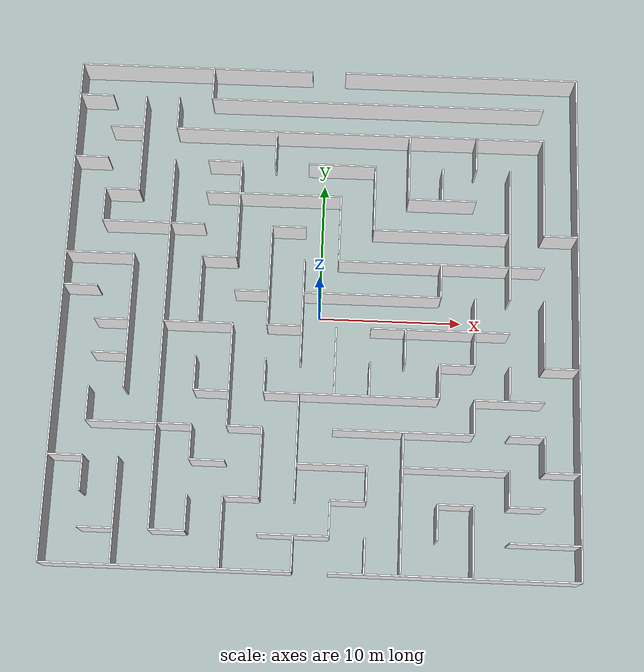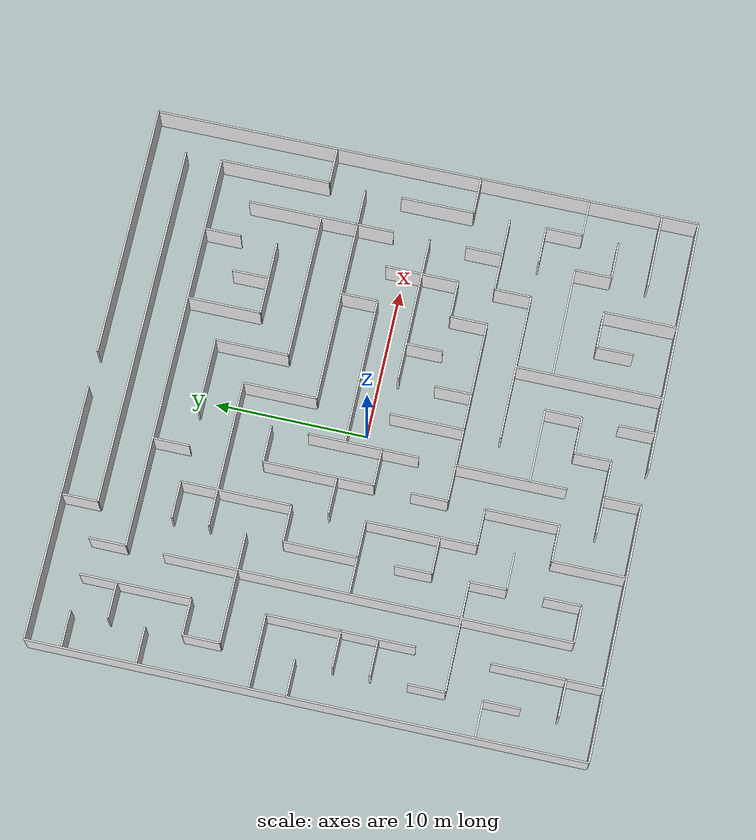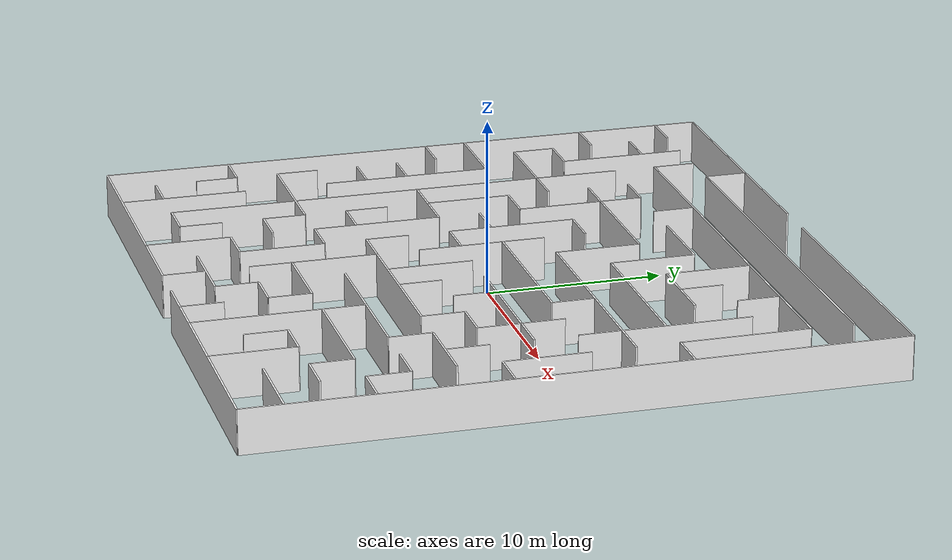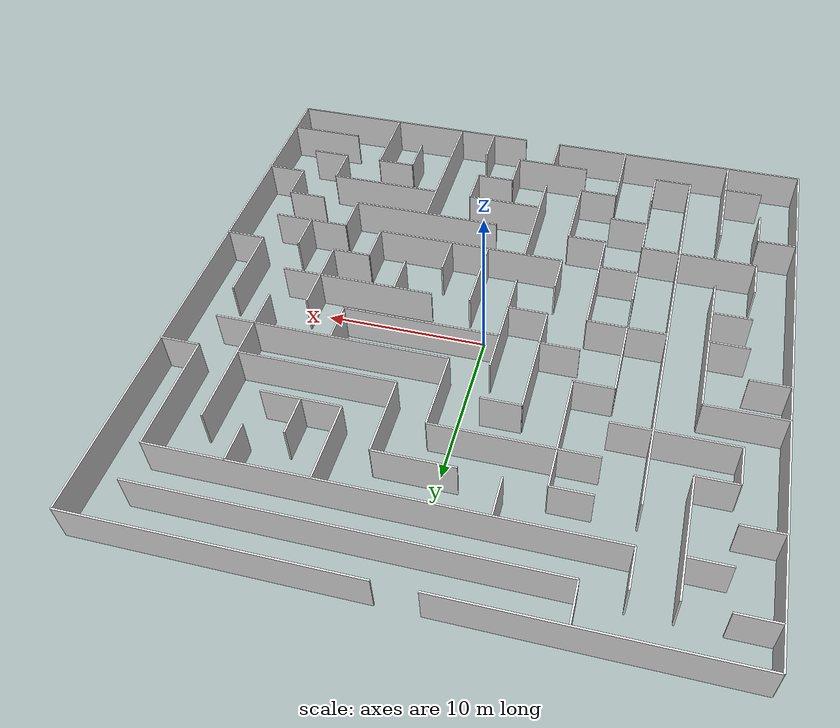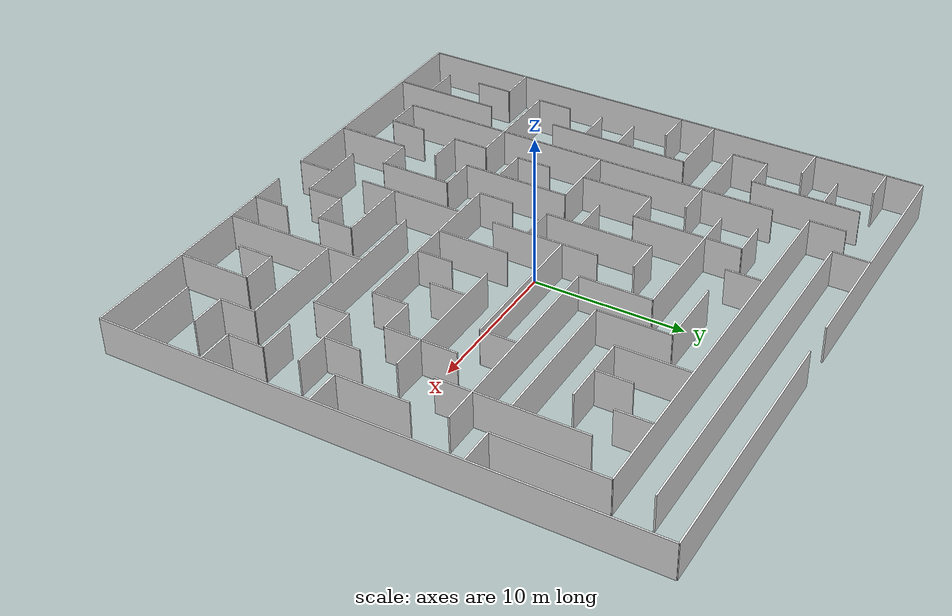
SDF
<?xml version='1.0'?>
<sdf version='1.7'>
  <model name='maze_3'>
    <pose>0 0 0 0 -0 0</pose>
    <static>1</static>
    <link name='Wall_0'>
      <collision name='Wall_0_Collision'>
        <geometry>
          <box>
            <size>16.8000 0.1000 2.5000</size>
          </box>
        </geometry>
        <pose>0 0 1.2500 0 -0 0</pose>
        <max_contacts>10</max_contacts>
        <surface>
          <contact><ode/></contact>
          <bounce/>
          <friction><torsional><ode/></torsional><ode/></friction>
        </surface>
      </collision>
      <visual name='Wall_0_Visual'>
        <pose>0 0 1.2500 0 -0 0</pose>
        <geometry>
          <box>
            <size>16.8000 0.1000 2.5000</size>
          </box>
        </geometry>
        <material>
          <script>
            <uri>file://media/materials/scripts/gazebo.material</uri>
            <n>Gazebo/Grey</n>
          </script>
          <ambient>1 1 1 1</ambient>
        </material>
        <meta><layer>0</layer></meta>
      </visual>
      <pose>-9.600000 18.000000 0 0 -0 -0.00000</pose>
      <self_collide>0</self_collide>
      <enable_wind>0</enable_wind>
      <kinematic>0</kinematic>
    </link>
    <link name='Wall_1'>
      <collision name='Wall_1_Collision'>
        <geometry>
          <box>
            <size>16.8000 0.1000 2.5000</size>
          </box>
        </geometry>
        <pose>0 0 1.2500 0 -0 0</pose>
        <max_contacts>10</max_contacts>
        <surface>
          <contact><ode/></contact>
          <bounce/>
          <friction><torsional><ode/></torsional><ode/></friction>
        </surface>
      </collision>
      <visual name='Wall_1_Visual'>
        <pose>0 0 1.2500 0 -0 0</pose>
        <geometry>
          <box>
            <size>16.8000 0.1000 2.5000</size>
          </box>
        </geometry>
        <material>
          <script>
            <uri>file://media/materials/scripts/gazebo.material</uri>
            <n>Gazebo/Grey</n>
          </script>
          <ambient>1 1 1 1</ambient>
        </material>
        <meta><layer>0</layer></meta>
      </visual>
      <pose>9.600000 18.000000 0 0 -0 -0.00000</pose>
      <self_collide>0</self_collide>
      <enable_wind>0</enable_wind>
      <kinematic>0</kinematic>
    </link>
    <link name='Wall_2'>
      <collision name='Wall_2_Collision'>
        <geometry>
          <box>
            <size>2.4000 0.1000 2.5000</size>
          </box>
        </geometry>
        <pose>0 0 1.2500 0 -0 0</pose>
        <max_contacts>10</max_contacts>
        <surface>
          <contact><ode/></contact>
          <bounce/>
          <friction><torsional><ode/></torsional><ode/></friction>
        </surface>
      </collision>
      <visual name='Wall_2_Visual'>
        <pose>0 0 1.2500 0 -0 0</pose>
        <geometry>
          <box>
            <size>2.4000 0.1000 2.5000</size>
          </box>
        </geometry>
        <material>
          <script>
            <uri>file://media/materials/scripts/gazebo.material</uri>
            <n>Gazebo/Grey</n>
          </script>
          <ambient>1 1 1 1</ambient>
        </material>
        <meta><layer>0</layer></meta>
      </visual>
      <pose>-16.800000 15.600000 0 0 -0 -0.00000</pose>
      <self_collide>0</self_collide>
      <enable_wind>0</enable_wind>
      <kinematic>0</kinematic>
    </link>
    <link name='Wall_3'>
      <collision name='Wall_3_Collision'>
        <geometry>
          <box>
            <size>24.0000 0.1000 2.5000</size>
          </box>
        </geometry>
        <pose>0 0 1.2500 0 -0 0</pose>
        <max_contacts>10</max_contacts>
        <surface>
          <contact><ode/></contact>
          <bounce/>
          <friction><torsional><ode/></torsional><ode/></friction>
        </surface>
      </collision>
      <visual name='Wall_3_Visual'>
        <pose>0 0 1.2500 0 -0 0</pose>
        <geometry>
          <box>
            <size>24.0000 0.1000 2.5000</size>
          </box>
        </geometry>
        <material>
          <script>
            <uri>file://media/materials/scripts/gazebo.material</uri>
            <n>Gazebo/Grey</n>
          </script>
          <ambient>1 1 1 1</ambient>
        </material>
        <meta><layer>0</layer></meta>
      </visual>
      <pose>3.600000 15.600000 0 0 -0 -0.00000</pose>
      <self_collide>0</self_collide>
      <enable_wind>0</enable_wind>
      <kinematic>0</kinematic>
    </link>
    <link name='Wall_4'>
      <collision name='Wall_4_Collision'>
        <geometry>
          <box>
            <size>2.4000 0.1000 2.5000</size>
          </box>
        </geometry>
        <pose>0 0 1.2500 0 -0 0</pose>
        <max_contacts>10</max_contacts>
        <surface>
          <contact><ode/></contact>
          <bounce/>
          <friction><torsional><ode/></torsional><ode/></friction>
        </surface>
      </collision>
      <visual name='Wall_4_Visual'>
        <pose>0 0 1.2500 0 -0 0</pose>
        <geometry>
          <box>
            <size>2.4000 0.1000 2.5000</size>
          </box>
        </geometry>
        <material>
          <script>
            <uri>file://media/materials/scripts/gazebo.material</uri>
            <n>Gazebo/Grey</n>
          </script>
          <ambient>1 1 1 1</ambient>
        </material>
        <meta><layer>0</layer></meta>
      </visual>
      <pose>-14.400000 13.200000 0 0 -0 -0.00000</pose>
      <self_collide>0</self_collide>
      <enable_wind>0</enable_wind>
      <kinematic>0</kinematic>
    </link>
    <link name='Wall_5'>
      <collision name='Wall_5_Collision'>
        <geometry>
          <box>
            <size>26.4000 0.1000 2.5000</size>
          </box>
        </geometry>
        <pose>0 0 1.2500 0 -0 0</pose>
        <max_contacts>10</max_contacts>
        <surface>
          <contact><ode/></contact>
          <bounce/>
          <friction><torsional><ode/></torsional><ode/></friction>
        </surface>
      </collision>
      <visual name='Wall_5_Visual'>
        <pose>0 0 1.2500 0 -0 0</pose>
        <geometry>
          <box>
            <size>26.4000 0.1000 2.5000</size>
          </box>
        </geometry>
        <material>
          <script>
            <uri>file://media/materials/scripts/gazebo.material</uri>
            <n>Gazebo/Grey</n>
          </script>
          <ambient>1 1 1 1</ambient>
        </material>
        <meta><layer>0</layer></meta>
      </visual>
      <pose>2.400000 13.200000 0 0 -0 -0.00000</pose>
      <self_collide>0</self_collide>
      <enable_wind>0</enable_wind>
      <kinematic>0</kinematic>
    </link>
    <link name='Wall_6'>
      <collision name='Wall_6_Collision'>
        <geometry>
          <box>
            <size>2.4000 0.1000 2.5000</size>
          </box>
        </geometry>
        <pose>0 0 1.2500 0 -0 0</pose>
        <max_contacts>10</max_contacts>
        <surface>
          <contact><ode/></contact>
          <bounce/>
          <friction><torsional><ode/></torsional><ode/></friction>
        </surface>
      </collision>
      <visual name='Wall_6_Visual'>
        <pose>0 0 1.2500 0 -0 0</pose>
        <geometry>
          <box>
            <size>2.4000 0.1000 2.5000</size>
          </box>
        </geometry>
        <material>
          <script>
            <uri>file://media/materials/scripts/gazebo.material</uri>
            <n>Gazebo/Grey</n>
          </script>
          <ambient>1 1 1 1</ambient>
        </material>
        <meta><layer>0</layer></meta>
      </visual>
      <pose>-16.800000 10.800000 0 0 -0 -0.00000</pose>
      <self_collide>0</self_collide>
      <enable_wind>0</enable_wind>
      <kinematic>0</kinematic>
    </link>
    <link name='Wall_7'>
      <collision name='Wall_7_Collision'>
        <geometry>
          <box>
            <size>2.4000 0.1000 2.5000</size>
          </box>
        </geometry>
        <pose>0 0 1.2500 0 -0 0</pose>
        <max_contacts>10</max_contacts>
        <surface>
          <contact><ode/></contact>
          <bounce/>
          <friction><torsional><ode/></torsional><ode/></friction>
        </surface>
      </collision>
      <visual name='Wall_7_Visual'>
        <pose>0 0 1.2500 0 -0 0</pose>
        <geometry>
          <box>
            <size>2.4000 0.1000 2.5000</size>
          </box>
        </geometry>
        <material>
          <script>
            <uri>file://media/materials/scripts/gazebo.material</uri>
            <n>Gazebo/Grey</n>
          </script>
          <ambient>1 1 1 1</ambient>
        </material>
        <meta><layer>0</layer></meta>
      </visual>
      <pose>-7.200000 10.800000 0 0 -0 -0.00000</pose>
      <self_collide>0</self_collide>
      <enable_wind>0</enable_wind>
      <kinematic>0</kinematic>
    </link>
    <link name='Wall_8'>
      <collision name='Wall_8_Collision'>
        <geometry>
          <box>
            <size>4.8000 0.1000 2.5000</size>
          </box>
        </geometry>
        <pose>0 0 1.2500 0 -0 0</pose>
        <max_contacts>10</max_contacts>
        <surface>
          <contact><ode/></contact>
          <bounce/>
          <friction><torsional><ode/></torsional><ode/></friction>
        </surface>
      </collision>
      <visual name='Wall_8_Visual'>
        <pose>0 0 1.2500 0 -0 0</pose>
        <geometry>
          <box>
            <size>4.8000 0.1000 2.5000</size>
          </box>
        </geometry>
        <material>
          <script>
            <uri>file://media/materials/scripts/gazebo.material</uri>
            <n>Gazebo/Grey</n>
          </script>
          <ambient>1 1 1 1</ambient>
        </material>
        <meta><layer>0</layer></meta>
      </visual>
      <pose>1.200000 10.800000 0 0 -0 -0.00000</pose>
      <self_collide>0</self_collide>
      <enable_wind>0</enable_wind>
      <kinematic>0</kinematic>
    </link>
    <link name='Wall_9'>
      <collision name='Wall_9_Collision'>
        <geometry>
          <box>
            <size>2.4000 0.1000 2.5000</size>
          </box>
        </geometry>
        <pose>0 0 1.2500 0 -0 0</pose>
        <max_contacts>10</max_contacts>
        <surface>
          <contact><ode/></contact>
          <bounce/>
          <friction><torsional><ode/></torsional><ode/></friction>
        </surface>
      </collision>
      <visual name='Wall_9_Visual'>
        <pose>0 0 1.2500 0 -0 0</pose>
        <geometry>
          <box>
            <size>2.4000 0.1000 2.5000</size>
          </box>
        </geometry>
        <material>
          <script>
            <uri>file://media/materials/scripts/gazebo.material</uri>
            <n>Gazebo/Grey</n>
          </script>
          <ambient>1 1 1 1</ambient>
        </material>
        <meta><layer>0</layer></meta>
      </visual>
      <pose>-14.400000 8.400000 0 0 -0 -0.00000</pose>
      <self_collide>0</self_collide>
      <enable_wind>0</enable_wind>
      <kinematic>0</kinematic>
    </link>
    <link name='Wall_10'>
      <collision name='Wall_10_Collision'>
        <geometry>
          <box>
            <size>9.6000 0.1000 2.5000</size>
          </box>
        </geometry>
        <pose>0 0 1.2500 0 -0 0</pose>
        <max_contacts>10</max_contacts>
        <surface>
          <contact><ode/></contact>
          <bounce/>
          <friction><torsional><ode/></torsional><ode/></friction>
        </surface>
      </collision>
      <visual name='Wall_10_Visual'>
        <pose>0 0 1.2500 0 -0 0</pose>
        <geometry>
          <box>
            <size>9.6000 0.1000 2.5000</size>
          </box>
        </geometry>
        <material>
          <script>
            <uri>file://media/materials/scripts/gazebo.material</uri>
            <n>Gazebo/Grey</n>
          </script>
          <ambient>1 1 1 1</ambient>
        </material>
        <meta><layer>0</layer></meta>
      </visual>
      <pose>-3.600000 8.400000 0 0 -0 -0.00000</pose>
      <self_collide>0</self_collide>
      <enable_wind>0</enable_wind>
      <kinematic>0</kinematic>
    </link>
    <link name='Wall_11'>
      <collision name='Wall_11_Collision'>
        <geometry>
          <box>
            <size>4.8000 0.1000 2.5000</size>
          </box>
        </geometry>
        <pose>0 0 1.2500 0 -0 0</pose>
        <max_contacts>10</max_contacts>
        <surface>
          <contact><ode/></contact>
          <bounce/>
          <friction><torsional><ode/></torsional><ode/></friction>
        </surface>
      </collision>
      <visual name='Wall_11_Visual'>
        <pose>0 0 1.2500 0 -0 0</pose>
        <geometry>
          <box>
            <size>4.8000 0.1000 2.5000</size>
          </box>
        </geometry>
        <material>
          <script>
            <uri>file://media/materials/scripts/gazebo.material</uri>
            <n>Gazebo/Grey</n>
          </script>
          <ambient>1 1 1 1</ambient>
        </material>
        <meta><layer>0</layer></meta>
      </visual>
      <pose>8.400000 8.400000 0 0 -0 -0.00000</pose>
      <self_collide>0</self_collide>
      <enable_wind>0</enable_wind>
      <kinematic>0</kinematic>
    </link>
    <link name='Wall_12'>
      <collision name='Wall_12_Collision'>
        <geometry>
          <box>
            <size>7.2000 0.1000 2.5000</size>
          </box>
        </geometry>
        <pose>0 0 1.2500 0 -0 0</pose>
        <max_contacts>10</max_contacts>
        <surface>
          <contact><ode/></contact>
          <bounce/>
          <friction><torsional><ode/></torsional><ode/></friction>
        </surface>
      </collision>
      <visual name='Wall_12_Visual'>
        <pose>0 0 1.2500 0 -0 0</pose>
        <geometry>
          <box>
            <size>7.2000 0.1000 2.5000</size>
          </box>
        </geometry>
        <material>
          <script>
            <uri>file://media/materials/scripts/gazebo.material</uri>
            <n>Gazebo/Grey</n>
          </script>
          <ambient>1 1 1 1</ambient>
        </material>
        <meta><layer>0</layer></meta>
      </visual>
      <pose>-12.000000 6.000000 0 0 -0 -0.00000</pose>
      <self_collide>0</self_collide>
      <enable_wind>0</enable_wind>
      <kinematic>0</kinematic>
    </link>
    <link name='Wall_13'>
      <collision name='Wall_13_Collision'>
        <geometry>
          <box>
            <size>2.4000 0.1000 2.5000</size>
          </box>
        </geometry>
        <pose>0 0 1.2500 0 -0 0</pose>
        <max_contacts>10</max_contacts>
        <surface>
          <contact><ode/></contact>
          <bounce/>
          <friction><torsional><ode/></torsional><ode/></friction>
        </surface>
      </collision>
      <visual name='Wall_13_Visual'>
        <pose>0 0 1.2500 0 -0 0</pose>
        <geometry>
          <box>
            <size>2.4000 0.1000 2.5000</size>
          </box>
        </geometry>
        <material>
          <script>
            <uri>file://media/materials/scripts/gazebo.material</uri>
            <n>Gazebo/Grey</n>
          </script>
          <ambient>1 1 1 1</ambient>
        </material>
        <meta><layer>0</layer></meta>
      </visual>
      <pose>-2.400000 6.000000 0 0 -0 -0.00000</pose>
      <self_collide>0</self_collide>
      <enable_wind>0</enable_wind>
      <kinematic>0</kinematic>
    </link>
    <link name='Wall_14'>
      <collision name='Wall_14_Collision'>
        <geometry>
          <box>
            <size>9.6000 0.1000 2.5000</size>
          </box>
        </geometry>
        <pose>0 0 1.2500 0 -0 0</pose>
        <max_contacts>10</max_contacts>
        <surface>
          <contact><ode/></contact>
          <bounce/>
          <friction><torsional><ode/></torsional><ode/></friction>
        </surface>
      </collision>
      <visual name='Wall_14_Visual'>
        <pose>0 0 1.2500 0 -0 0</pose>
        <geometry>
          <box>
            <size>9.6000 0.1000 2.5000</size>
          </box>
        </geometry>
        <material>
          <script>
            <uri>file://media/materials/scripts/gazebo.material</uri>
            <n>Gazebo/Grey</n>
          </script>
          <ambient>1 1 1 1</ambient>
        </material>
        <meta><layer>0</layer></meta>
      </visual>
      <pose>8.400000 6.000000 0 0 -0 -0.00000</pose>
      <self_collide>0</self_collide>
      <enable_wind>0</enable_wind>
      <kinematic>0</kinematic>
    </link>
    <link name='Wall_15'>
      <collision name='Wall_15_Collision'>
        <geometry>
          <box>
            <size>2.4000 0.1000 2.5000</size>
          </box>
        </geometry>
        <pose>0 0 1.2500 0 -0 0</pose>
        <max_contacts>10</max_contacts>
        <surface>
          <contact><ode/></contact>
          <bounce/>
          <friction><torsional><ode/></torsional><ode/></friction>
        </surface>
      </collision>
      <visual name='Wall_15_Visual'>
        <pose>0 0 1.2500 0 -0 0</pose>
        <geometry>
          <box>
            <size>2.4000 0.1000 2.5000</size>
          </box>
        </geometry>
        <material>
          <script>
            <uri>file://media/materials/scripts/gazebo.material</uri>
            <n>Gazebo/Grey</n>
          </script>
          <ambient>1 1 1 1</ambient>
        </material>
        <meta><layer>0</layer></meta>
      </visual>
      <pose>16.800000 6.000000 0 0 -0 -0.00000</pose>
      <self_collide>0</self_collide>
      <enable_wind>0</enable_wind>
      <kinematic>0</kinematic>
    </link>
    <link name='Wall_16'>
      <collision name='Wall_16_Collision'>
        <geometry>
          <box>
            <size>4.8000 0.1000 2.5000</size>
          </box>
        </geometry>
        <pose>0 0 1.2500 0 -0 0</pose>
        <max_contacts>10</max_contacts>
        <surface>
          <contact><ode/></contact>
          <bounce/>
          <friction><torsional><ode/></torsional><ode/></friction>
        </surface>
      </collision>
      <visual name='Wall_16_Visual'>
        <pose>0 0 1.2500 0 -0 0</pose>
        <geometry>
          <box>
            <size>4.8000 0.1000 2.5000</size>
          </box>
        </geometry>
        <material>
          <script>
            <uri>file://media/materials/scripts/gazebo.material</uri>
            <n>Gazebo/Grey</n>
          </script>
          <ambient>1 1 1 1</ambient>
        </material>
        <meta><layer>0</layer></meta>
      </visual>
      <pose>-15.600000 3.600000 0 0 -0 -0.00000</pose>
      <self_collide>0</self_collide>
      <enable_wind>0</enable_wind>
      <kinematic>0</kinematic>
    </link>
    <link name='Wall_17'>
      <collision name='Wall_17_Collision'>
        <geometry>
          <box>
            <size>2.4000 0.1000 2.5000</size>
          </box>
        </geometry>
        <pose>0 0 1.2500 0 -0 0</pose>
        <max_contacts>10</max_contacts>
        <surface>
          <contact><ode/></contact>
          <bounce/>
          <friction><torsional><ode/></torsional><ode/></friction>
        </surface>
      </collision>
      <visual name='Wall_17_Visual'>
        <pose>0 0 1.2500 0 -0 0</pose>
        <geometry>
          <box>
            <size>2.4000 0.1000 2.5000</size>
          </box>
        </geometry>
        <material>
          <script>
            <uri>file://media/materials/scripts/gazebo.material</uri>
            <n>Gazebo/Grey</n>
          </script>
          <ambient>1 1 1 1</ambient>
        </material>
        <meta><layer>0</layer></meta>
      </visual>
      <pose>-7.200000 3.600000 0 0 -0 -0.00000</pose>
      <self_collide>0</self_collide>
      <enable_wind>0</enable_wind>
      <kinematic>0</kinematic>
    </link>
    <link name='Wall_18'>
      <collision name='Wall_18_Collision'>
        <geometry>
          <box>
            <size>14.4000 0.1000 2.5000</size>
          </box>
        </geometry>
        <pose>0 0 1.2500 0 -0 0</pose>
        <max_contacts>10</max_contacts>
        <surface>
          <contact><ode/></contact>
          <bounce/>
          <friction><torsional><ode/></torsional><ode/></friction>
        </surface>
      </collision>
      <visual name='Wall_18_Visual'>
        <pose>0 0 1.2500 0 -0 0</pose>
        <geometry>
          <box>
            <size>14.4000 0.1000 2.5000</size>
          </box>
        </geometry>
        <material>
          <script>
            <uri>file://media/materials/scripts/gazebo.material</uri>
            <n>Gazebo/Grey</n>
          </script>
          <ambient>1 1 1 1</ambient>
        </material>
        <meta><layer>0</layer></meta>
      </visual>
      <pose>8.400000 3.600000 0 0 -0 -0.00000</pose>
      <self_collide>0</self_collide>
      <enable_wind>0</enable_wind>
      <kinematic>0</kinematic>
    </link>
    <link name='Wall_19'>
      <collision name='Wall_19_Collision'>
        <geometry>
          <box>
            <size>2.4000 0.1000 2.5000</size>
          </box>
        </geometry>
        <pose>0 0 1.2500 0 -0 0</pose>
        <max_contacts>10</max_contacts>
        <surface>
          <contact><ode/></contact>
          <bounce/>
          <friction><torsional><ode/></torsional><ode/></friction>
        </surface>
      </collision>
      <visual name='Wall_19_Visual'>
        <pose>0 0 1.2500 0 -0 0</pose>
        <geometry>
          <box>
            <size>2.4000 0.1000 2.5000</size>
          </box>
        </geometry>
        <material>
          <script>
            <uri>file://media/materials/scripts/gazebo.material</uri>
            <n>Gazebo/Grey</n>
          </script>
          <ambient>1 1 1 1</ambient>
        </material>
        <meta><layer>0</layer></meta>
      </visual>
      <pose>-16.800000 1.200000 0 0 -0 -0.00000</pose>
      <self_collide>0</self_collide>
      <enable_wind>0</enable_wind>
      <kinematic>0</kinematic>
    </link>
    <link name='Wall_20'>
      <collision name='Wall_20_Collision'>
        <geometry>
          <box>
            <size>2.4000 0.1000 2.5000</size>
          </box>
        </geometry>
        <pose>0 0 1.2500 0 -0 0</pose>
        <max_contacts>10</max_contacts>
        <surface>
          <contact><ode/></contact>
          <bounce/>
          <friction><torsional><ode/></torsional><ode/></friction>
        </surface>
      </collision>
      <visual name='Wall_20_Visual'>
        <pose>0 0 1.2500 0 -0 0</pose>
        <geometry>
          <box>
            <size>2.4000 0.1000 2.5000</size>
          </box>
        </geometry>
        <material>
          <script>
            <uri>file://media/materials/scripts/gazebo.material</uri>
            <n>Gazebo/Grey</n>
          </script>
          <ambient>1 1 1 1</ambient>
        </material>
        <meta><layer>0</layer></meta>
      </visual>
      <pose>-4.800000 1.200000 0 0 -0 -0.00000</pose>
      <self_collide>0</self_collide>
      <enable_wind>0</enable_wind>
      <kinematic>0</kinematic>
    </link>
    <link name='Wall_21'>
      <collision name='Wall_21_Collision'>
        <geometry>
          <box>
            <size>9.6000 0.1000 2.5000</size>
          </box>
        </geometry>
        <pose>0 0 1.2500 0 -0 0</pose>
        <max_contacts>10</max_contacts>
        <surface>
          <contact><ode/></contact>
          <bounce/>
          <friction><torsional><ode/></torsional><ode/></friction>
        </surface>
      </collision>
      <visual name='Wall_21_Visual'>
        <pose>0 0 1.2500 0 -0 0</pose>
        <geometry>
          <box>
            <size>9.6000 0.1000 2.5000</size>
          </box>
        </geometry>
        <material>
          <script>
            <uri>file://media/materials/scripts/gazebo.material</uri>
            <n>Gazebo/Grey</n>
          </script>
          <ambient>1 1 1 1</ambient>
        </material>
        <meta><layer>0</layer></meta>
      </visual>
      <pose>3.600000 1.200000 0 0 -0 -0.00000</pose>
      <self_collide>0</self_collide>
      <enable_wind>0</enable_wind>
      <kinematic>0</kinematic>
    </link>
    <link name='Wall_22'>
      <collision name='Wall_22_Collision'>
        <geometry>
          <box>
            <size>2.4000 0.1000 2.5000</size>
          </box>
        </geometry>
        <pose>0 0 1.2500 0 -0 0</pose>
        <max_contacts>10</max_contacts>
        <surface>
          <contact><ode/></contact>
          <bounce/>
          <friction><torsional><ode/></torsional><ode/></friction>
        </surface>
      </collision>
      <visual name='Wall_22_Visual'>
        <pose>0 0 1.2500 0 -0 0</pose>
        <geometry>
          <box>
            <size>2.4000 0.1000 2.5000</size>
          </box>
        </geometry>
        <material>
          <script>
            <uri>file://media/materials/scripts/gazebo.material</uri>
            <n>Gazebo/Grey</n>
          </script>
          <ambient>1 1 1 1</ambient>
        </material>
        <meta><layer>0</layer></meta>
      </visual>
      <pose>-14.400000 -1.200000 0 0 -0 -0.00000</pose>
      <self_collide>0</self_collide>
      <enable_wind>0</enable_wind>
      <kinematic>0</kinematic>
    </link>
    <link name='Wall_23'>
      <collision name='Wall_23_Collision'>
        <geometry>
          <box>
            <size>4.8000 0.1000 2.5000</size>
          </box>
        </geometry>
        <pose>0 0 1.2500 0 -0 0</pose>
        <max_contacts>10</max_contacts>
        <surface>
          <contact><ode/></contact>
          <bounce/>
          <friction><torsional><ode/></torsional><ode/></friction>
        </surface>
      </collision>
      <visual name='Wall_23_Visual'>
        <pose>0 0 1.2500 0 -0 0</pose>
        <geometry>
          <box>
            <size>4.8000 0.1000 2.5000</size>
          </box>
        </geometry>
        <material>
          <script>
            <uri>file://media/materials/scripts/gazebo.material</uri>
            <n>Gazebo/Grey</n>
          </script>
          <ambient>1 1 1 1</ambient>
        </material>
        <meta><layer>0</layer></meta>
      </visual>
      <pose>-8.400000 -1.200000 0 0 -0 -0.00000</pose>
      <self_collide>0</self_collide>
      <enable_wind>0</enable_wind>
      <kinematic>0</kinematic>
    </link>
    <link name='Wall_24'>
      <collision name='Wall_24_Collision'>
        <geometry>
          <box>
            <size>2.4000 0.1000 2.5000</size>
          </box>
        </geometry>
        <pose>0 0 1.2500 0 -0 0</pose>
        <max_contacts>10</max_contacts>
        <surface>
          <contact><ode/></contact>
          <bounce/>
          <friction><torsional><ode/></torsional><ode/></friction>
        </surface>
      </collision>
      <visual name='Wall_24_Visual'>
        <pose>0 0 1.2500 0 -0 0</pose>
        <geometry>
          <box>
            <size>2.4000 0.1000 2.5000</size>
          </box>
        </geometry>
        <material>
          <script>
            <uri>file://media/materials/scripts/gazebo.material</uri>
            <n>Gazebo/Grey</n>
          </script>
          <ambient>1 1 1 1</ambient>
        </material>
        <meta><layer>0</layer></meta>
      </visual>
      <pose>-2.400000 -1.200000 0 0 -0 -0.00000</pose>
      <self_collide>0</self_collide>
      <enable_wind>0</enable_wind>
      <kinematic>0</kinematic>
    </link>
    <link name='Wall_25'>
      <collision name='Wall_25_Collision'>
        <geometry>
          <box>
            <size>9.6000 0.1000 2.5000</size>
          </box>
        </geometry>
        <pose>0 0 1.2500 0 -0 0</pose>
        <max_contacts>10</max_contacts>
        <surface>
          <contact><ode/></contact>
          <bounce/>
          <friction><torsional><ode/></torsional><ode/></friction>
        </surface>
      </collision>
      <visual name='Wall_25_Visual'>
        <pose>0 0 1.2500 0 -0 0</pose>
        <geometry>
          <box>
            <size>9.6000 0.1000 2.5000</size>
          </box>
        </geometry>
        <material>
          <script>
            <uri>file://media/materials/scripts/gazebo.material</uri>
            <n>Gazebo/Grey</n>
          </script>
          <ambient>1 1 1 1</ambient>
        </material>
        <meta><layer>0</layer></meta>
      </visual>
      <pose>8.400000 -1.200000 0 0 -0 -0.00000</pose>
      <self_collide>0</self_collide>
      <enable_wind>0</enable_wind>
      <kinematic>0</kinematic>
    </link>
    <link name='Wall_26'>
      <collision name='Wall_26_Collision'>
        <geometry>
          <box>
            <size>2.4000 0.1000 2.5000</size>
          </box>
        </geometry>
        <pose>0 0 1.2500 0 -0 0</pose>
        <max_contacts>10</max_contacts>
        <surface>
          <contact><ode/></contact>
          <bounce/>
          <friction><torsional><ode/></torsional><ode/></friction>
        </surface>
      </collision>
      <visual name='Wall_26_Visual'>
        <pose>0 0 1.2500 0 -0 0</pose>
        <geometry>
          <box>
            <size>2.4000 0.1000 2.5000</size>
          </box>
        </geometry>
        <material>
          <script>
            <uri>file://media/materials/scripts/gazebo.material</uri>
            <n>Gazebo/Grey</n>
          </script>
          <ambient>1 1 1 1</ambient>
        </material>
        <meta><layer>0</layer></meta>
      </visual>
      <pose>-14.400000 -3.600000 0 0 -0 -0.00000</pose>
      <self_collide>0</self_collide>
      <enable_wind>0</enable_wind>
      <kinematic>0</kinematic>
    </link>
    <link name='Wall_27'>
      <collision name='Wall_27_Collision'>
        <geometry>
          <box>
            <size>2.4000 0.1000 2.5000</size>
          </box>
        </geometry>
        <pose>0 0 1.2500 0 -0 0</pose>
        <max_contacts>10</max_contacts>
        <surface>
          <contact><ode/></contact>
          <bounce/>
          <friction><torsional><ode/></torsional><ode/></friction>
        </surface>
      </collision>
      <visual name='Wall_27_Visual'>
        <pose>0 0 1.2500 0 -0 0</pose>
        <geometry>
          <box>
            <size>2.4000 0.1000 2.5000</size>
          </box>
        </geometry>
        <material>
          <script>
            <uri>file://media/materials/scripts/gazebo.material</uri>
            <n>Gazebo/Grey</n>
          </script>
          <ambient>1 1 1 1</ambient>
        </material>
        <meta><layer>0</layer></meta>
      </visual>
      <pose>9.600000 -3.600000 0 0 -0 -0.00000</pose>
      <self_collide>0</self_collide>
      <enable_wind>0</enable_wind>
      <kinematic>0</kinematic>
    </link>
    <link name='Wall_28'>
      <collision name='Wall_28_Collision'>
        <geometry>
          <box>
            <size>2.4000 0.1000 2.5000</size>
          </box>
        </geometry>
        <pose>0 0 1.2500 0 -0 0</pose>
        <max_contacts>10</max_contacts>
        <surface>
          <contact><ode/></contact>
          <bounce/>
          <friction><torsional><ode/></torsional><ode/></friction>
        </surface>
      </collision>
      <visual name='Wall_28_Visual'>
        <pose>0 0 1.2500 0 -0 0</pose>
        <geometry>
          <box>
            <size>2.4000 0.1000 2.5000</size>
          </box>
        </geometry>
        <material>
          <script>
            <uri>file://media/materials/scripts/gazebo.material</uri>
            <n>Gazebo/Grey</n>
          </script>
          <ambient>1 1 1 1</ambient>
        </material>
        <meta><layer>0</layer></meta>
      </visual>
      <pose>16.800000 -3.600000 0 0 -0 -0.00000</pose>
      <self_collide>0</self_collide>
      <enable_wind>0</enable_wind>
      <kinematic>0</kinematic>
    </link>
    <link name='Wall_29'>
      <collision name='Wall_29_Collision'>
        <geometry>
          <box>
            <size>2.4000 0.1000 2.5000</size>
          </box>
        </geometry>
        <pose>0 0 1.2500 0 -0 0</pose>
        <max_contacts>10</max_contacts>
        <surface>
          <contact><ode/></contact>
          <bounce/>
          <friction><torsional><ode/></torsional><ode/></friction>
        </surface>
      </collision>
      <visual name='Wall_29_Visual'>
        <pose>0 0 1.2500 0 -0 0</pose>
        <geometry>
          <box>
            <size>2.4000 0.1000 2.5000</size>
          </box>
        </geometry>
        <material>
          <script>
            <uri>file://media/materials/scripts/gazebo.material</uri>
            <n>Gazebo/Grey</n>
          </script>
          <ambient>1 1 1 1</ambient>
        </material>
        <meta><layer>0</layer></meta>
      </visual>
      <pose>-7.200000 -6.000000 0 0 -0 -0.00000</pose>
      <self_collide>0</self_collide>
      <enable_wind>0</enable_wind>
      <kinematic>0</kinematic>
    </link>
    <link name='Wall_30'>
      <collision name='Wall_30_Collision'>
        <geometry>
          <box>
            <size>12.0000 0.1000 2.5000</size>
          </box>
        </geometry>
        <pose>0 0 1.2500 0 -0 0</pose>
        <max_contacts>10</max_contacts>
        <surface>
          <contact><ode/></contact>
          <bounce/>
          <friction><torsional><ode/></torsional><ode/></friction>
        </surface>
      </collision>
      <visual name='Wall_30_Visual'>
        <pose>0 0 1.2500 0 -0 0</pose>
        <geometry>
          <box>
            <size>12.0000 0.1000 2.5000</size>
          </box>
        </geometry>
        <material>
          <script>
            <uri>file://media/materials/scripts/gazebo.material</uri>
            <n>Gazebo/Grey</n>
          </script>
          <ambient>1 1 1 1</ambient>
        </material>
        <meta><layer>0</layer></meta>
      </visual>
      <pose>2.400000 -6.000000 0 0 -0 -0.00000</pose>
      <self_collide>0</self_collide>
      <enable_wind>0</enable_wind>
      <kinematic>0</kinematic>
    </link>
    <link name='Wall_31'>
      <collision name='Wall_31_Collision'>
        <geometry>
          <box>
            <size>4.8000 0.1000 2.5000</size>
          </box>
        </geometry>
        <pose>0 0 1.2500 0 -0 0</pose>
        <max_contacts>10</max_contacts>
        <surface>
          <contact><ode/></contact>
          <bounce/>
          <friction><torsional><ode/></torsional><ode/></friction>
        </surface>
      </collision>
      <visual name='Wall_31_Visual'>
        <pose>0 0 1.2500 0 -0 0</pose>
        <geometry>
          <box>
            <size>4.8000 0.1000 2.5000</size>
          </box>
        </geometry>
        <material>
          <script>
            <uri>file://media/materials/scripts/gazebo.material</uri>
            <n>Gazebo/Grey</n>
          </script>
          <ambient>1 1 1 1</ambient>
        </material>
        <meta><layer>0</layer></meta>
      </visual>
      <pose>13.200000 -6.000000 0 0 -0 -0.00000</pose>
      <self_collide>0</self_collide>
      <enable_wind>0</enable_wind>
      <kinematic>0</kinematic>
    </link>
    <link name='Wall_32'>
      <collision name='Wall_32_Collision'>
        <geometry>
          <box>
            <size>7.2000 0.1000 2.5000</size>
          </box>
        </geometry>
        <pose>0 0 1.2500 0 -0 0</pose>
        <max_contacts>10</max_contacts>
        <surface>
          <contact><ode/></contact>
          <bounce/>
          <friction><torsional><ode/></torsional><ode/></friction>
        </surface>
      </collision>
      <visual name='Wall_32_Visual'>
        <pose>0 0 1.2500 0 -0 0</pose>
        <geometry>
          <box>
            <size>7.2000 0.1000 2.5000</size>
          </box>
        </geometry>
        <material>
          <script>
            <uri>file://media/materials/scripts/gazebo.material</uri>
            <n>Gazebo/Grey</n>
          </script>
          <ambient>1 1 1 1</ambient>
        </material>
        <meta><layer>0</layer></meta>
      </visual>
      <pose>-12.000000 -8.400000 0 0 -0 -0.00000</pose>
      <self_collide>0</self_collide>
      <enable_wind>0</enable_wind>
      <kinematic>0</kinematic>
    </link>
    <link name='Wall_33'>
      <collision name='Wall_33_Collision'>
        <geometry>
          <box>
            <size>2.4000 0.1000 2.5000</size>
          </box>
        </geometry>
        <pose>0 0 1.2500 0 -0 0</pose>
        <max_contacts>10</max_contacts>
        <surface>
          <contact><ode/></contact>
          <bounce/>
          <friction><torsional><ode/></torsional><ode/></friction>
        </surface>
      </collision>
      <visual name='Wall_33_Visual'>
        <pose>0 0 1.2500 0 -0 0</pose>
        <geometry>
          <box>
            <size>2.4000 0.1000 2.5000</size>
          </box>
        </geometry>
        <material>
          <script>
            <uri>file://media/materials/scripts/gazebo.material</uri>
            <n>Gazebo/Grey</n>
          </script>
          <ambient>1 1 1 1</ambient>
        </material>
        <meta><layer>0</layer></meta>
      </visual>
      <pose>-4.800000 -8.400000 0 0 -0 -0.00000</pose>
      <self_collide>0</self_collide>
      <enable_wind>0</enable_wind>
      <kinematic>0</kinematic>
    </link>
    <link name='Wall_34'>
      <collision name='Wall_34_Collision'>
        <geometry>
          <box>
            <size>9.6000 0.1000 2.5000</size>
          </box>
        </geometry>
        <pose>0 0 1.2500 0 -0 0</pose>
        <max_contacts>10</max_contacts>
        <surface>
          <contact><ode/></contact>
          <bounce/>
          <friction><torsional><ode/></torsional><ode/></friction>
        </surface>
      </collision>
      <visual name='Wall_34_Visual'>
        <pose>0 0 1.2500 0 -0 0</pose>
        <geometry>
          <box>
            <size>9.6000 0.1000 2.5000</size>
          </box>
        </geometry>
        <material>
          <script>
            <uri>file://media/materials/scripts/gazebo.material</uri>
            <n>Gazebo/Grey</n>
          </script>
          <ambient>1 1 1 1</ambient>
        </material>
        <meta><layer>0</layer></meta>
      </visual>
      <pose>6.000000 -8.400000 0 0 -0 -0.00000</pose>
      <self_collide>0</self_collide>
      <enable_wind>0</enable_wind>
      <kinematic>0</kinematic>
    </link>
    <link name='Wall_35'>
      <collision name='Wall_35_Collision'>
        <geometry>
          <box>
            <size>2.4000 0.1000 2.5000</size>
          </box>
        </geometry>
        <pose>0 0 1.2500 0 -0 0</pose>
        <max_contacts>10</max_contacts>
        <surface>
          <contact><ode/></contact>
          <bounce/>
          <friction><torsional><ode/></torsional><ode/></friction>
        </surface>
      </collision>
      <visual name='Wall_35_Visual'>
        <pose>0 0 1.2500 0 -0 0</pose>
        <geometry>
          <box>
            <size>2.4000 0.1000 2.5000</size>
          </box>
        </geometry>
        <material>
          <script>
            <uri>file://media/materials/scripts/gazebo.material</uri>
            <n>Gazebo/Grey</n>
          </script>
          <ambient>1 1 1 1</ambient>
        </material>
        <meta><layer>0</layer></meta>
      </visual>
      <pose>14.400000 -8.400000 0 0 -0 -0.00000</pose>
      <self_collide>0</self_collide>
      <enable_wind>0</enable_wind>
      <kinematic>0</kinematic>
    </link>
    <link name='Wall_36'>
      <collision name='Wall_36_Collision'>
        <geometry>
          <box>
            <size>2.4000 0.1000 2.5000</size>
          </box>
        </geometry>
        <pose>0 0 1.2500 0 -0 0</pose>
        <max_contacts>10</max_contacts>
        <surface>
          <contact><ode/></contact>
          <bounce/>
          <friction><torsional><ode/></torsional><ode/></friction>
        </surface>
      </collision>
      <visual name='Wall_36_Visual'>
        <pose>0 0 1.2500 0 -0 0</pose>
        <geometry>
          <box>
            <size>2.4000 0.1000 2.5000</size>
          </box>
        </geometry>
        <material>
          <script>
            <uri>file://media/materials/scripts/gazebo.material</uri>
            <n>Gazebo/Grey</n>
          </script>
          <ambient>1 1 1 1</ambient>
        </material>
        <meta><layer>0</layer></meta>
      </visual>
      <pose>-16.800000 -10.800000 0 0 -0 -0.00000</pose>
      <self_collide>0</self_collide>
      <enable_wind>0</enable_wind>
      <kinematic>0</kinematic>
    </link>
    <link name='Wall_37'>
      <collision name='Wall_37_Collision'>
        <geometry>
          <box>
            <size>2.4000 0.1000 2.5000</size>
          </box>
        </geometry>
        <pose>0 0 1.2500 0 -0 0</pose>
        <max_contacts>10</max_contacts>
        <surface>
          <contact><ode/></contact>
          <bounce/>
          <friction><torsional><ode/></torsional><ode/></friction>
        </surface>
      </collision>
      <visual name='Wall_37_Visual'>
        <pose>0 0 1.2500 0 -0 0</pose>
        <geometry>
          <box>
            <size>2.4000 0.1000 2.5000</size>
          </box>
        </geometry>
        <material>
          <script>
            <uri>file://media/materials/scripts/gazebo.material</uri>
            <n>Gazebo/Grey</n>
          </script>
          <ambient>1 1 1 1</ambient>
        </material>
        <meta><layer>0</layer></meta>
      </visual>
      <pose>-7.200000 -10.800000 0 0 -0 -0.00000</pose>
      <self_collide>0</self_collide>
      <enable_wind>0</enable_wind>
      <kinematic>0</kinematic>
    </link>
    <link name='Wall_38'>
      <collision name='Wall_38_Collision'>
        <geometry>
          <box>
            <size>4.8000 0.1000 2.5000</size>
          </box>
        </geometry>
        <pose>0 0 1.2500 0 -0 0</pose>
        <max_contacts>10</max_contacts>
        <surface>
          <contact><ode/></contact>
          <bounce/>
          <friction><torsional><ode/></torsional><ode/></friction>
        </surface>
      </collision>
      <visual name='Wall_38_Visual'>
        <pose>0 0 1.2500 0 -0 0</pose>
        <geometry>
          <box>
            <size>4.8000 0.1000 2.5000</size>
          </box>
        </geometry>
        <material>
          <script>
            <uri>file://media/materials/scripts/gazebo.material</uri>
            <n>Gazebo/Grey</n>
          </script>
          <ambient>1 1 1 1</ambient>
        </material>
        <meta><layer>0</layer></meta>
      </visual>
      <pose>1.200000 -10.800000 0 0 -0 -0.00000</pose>
      <self_collide>0</self_collide>
      <enable_wind>0</enable_wind>
      <kinematic>0</kinematic>
    </link>
    <link name='Wall_39'>
      <collision name='Wall_39_Collision'>
        <geometry>
          <box>
            <size>7.2000 0.1000 2.5000</size>
          </box>
        </geometry>
        <pose>0 0 1.2500 0 -0 0</pose>
        <max_contacts>10</max_contacts>
        <surface>
          <contact><ode/></contact>
          <bounce/>
          <friction><torsional><ode/></torsional><ode/></friction>
        </surface>
      </collision>
      <visual name='Wall_39_Visual'>
        <pose>0 0 1.2500 0 -0 0</pose>
        <geometry>
          <box>
            <size>7.2000 0.1000 2.5000</size>
          </box>
        </geometry>
        <material>
          <script>
            <uri>file://media/materials/scripts/gazebo.material</uri>
            <n>Gazebo/Grey</n>
          </script>
          <ambient>1 1 1 1</ambient>
        </material>
        <meta><layer>0</layer></meta>
      </visual>
      <pose>9.600000 -10.800000 0 0 -0 -0.00000</pose>
      <self_collide>0</self_collide>
      <enable_wind>0</enable_wind>
      <kinematic>0</kinematic>
    </link>
    <link name='Wall_40'>
      <collision name='Wall_40_Collision'>
        <geometry>
          <box>
            <size>2.4000 0.1000 2.5000</size>
          </box>
        </geometry>
        <pose>0 0 1.2500 0 -0 0</pose>
        <max_contacts>10</max_contacts>
        <surface>
          <contact><ode/></contact>
          <bounce/>
          <friction><torsional><ode/></torsional><ode/></friction>
        </surface>
      </collision>
      <visual name='Wall_40_Visual'>
        <pose>0 0 1.2500 0 -0 0</pose>
        <geometry>
          <box>
            <size>2.4000 0.1000 2.5000</size>
          </box>
        </geometry>
        <material>
          <script>
            <uri>file://media/materials/scripts/gazebo.material</uri>
            <n>Gazebo/Grey</n>
          </script>
          <ambient>1 1 1 1</ambient>
        </material>
        <meta><layer>0</layer></meta>
      </visual>
      <pose>16.800000 -10.800000 0 0 -0 -0.00000</pose>
      <self_collide>0</self_collide>
      <enable_wind>0</enable_wind>
      <kinematic>0</kinematic>
    </link>
    <link name='Wall_41'>
      <collision name='Wall_41_Collision'>
        <geometry>
          <box>
            <size>2.4000 0.1000 2.5000</size>
          </box>
        </geometry>
        <pose>0 0 1.2500 0 -0 0</pose>
        <max_contacts>10</max_contacts>
        <surface>
          <contact><ode/></contact>
          <bounce/>
          <friction><torsional><ode/></torsional><ode/></friction>
        </surface>
      </collision>
      <visual name='Wall_41_Visual'>
        <pose>0 0 1.2500 0 -0 0</pose>
        <geometry>
          <box>
            <size>2.4000 0.1000 2.5000</size>
          </box>
        </geometry>
        <material>
          <script>
            <uri>file://media/materials/scripts/gazebo.material</uri>
            <n>Gazebo/Grey</n>
          </script>
          <ambient>1 1 1 1</ambient>
        </material>
        <meta><layer>0</layer></meta>
      </visual>
      <pose>-4.800000 -13.200000 0 0 -0 -0.00000</pose>
      <self_collide>0</self_collide>
      <enable_wind>0</enable_wind>
      <kinematic>0</kinematic>
    </link>
    <link name='Wall_42'>
      <collision name='Wall_42_Collision'>
        <geometry>
          <box>
            <size>2.4000 0.1000 2.5000</size>
          </box>
        </geometry>
        <pose>0 0 1.2500 0 -0 0</pose>
        <max_contacts>10</max_contacts>
        <surface>
          <contact><ode/></contact>
          <bounce/>
          <friction><torsional><ode/></torsional><ode/></friction>
        </surface>
      </collision>
      <visual name='Wall_42_Visual'>
        <pose>0 0 1.2500 0 -0 0</pose>
        <geometry>
          <box>
            <size>2.4000 0.1000 2.5000</size>
          </box>
        </geometry>
        <material>
          <script>
            <uri>file://media/materials/scripts/gazebo.material</uri>
            <n>Gazebo/Grey</n>
          </script>
          <ambient>1 1 1 1</ambient>
        </material>
        <meta><layer>0</layer></meta>
      </visual>
      <pose>2.400000 -13.200000 0 0 -0 -0.00000</pose>
      <self_collide>0</self_collide>
      <enable_wind>0</enable_wind>
      <kinematic>0</kinematic>
    </link>
    <link name='Wall_43'>
      <collision name='Wall_43_Collision'>
        <geometry>
          <box>
            <size>2.4000 0.1000 2.5000</size>
          </box>
        </geometry>
        <pose>0 0 1.2500 0 -0 0</pose>
        <max_contacts>10</max_contacts>
        <surface>
          <contact><ode/></contact>
          <bounce/>
          <friction><torsional><ode/></torsional><ode/></friction>
        </surface>
      </collision>
      <visual name='Wall_43_Visual'>
        <pose>0 0 1.2500 0 -0 0</pose>
        <geometry>
          <box>
            <size>2.4000 0.1000 2.5000</size>
          </box>
        </geometry>
        <material>
          <script>
            <uri>file://media/materials/scripts/gazebo.material</uri>
            <n>Gazebo/Grey</n>
          </script>
          <ambient>1 1 1 1</ambient>
        </material>
        <meta><layer>0</layer></meta>
      </visual>
      <pose>9.600000 -13.200000 0 0 -0 -0.00000</pose>
      <self_collide>0</self_collide>
      <enable_wind>0</enable_wind>
      <kinematic>0</kinematic>
    </link>
    <link name='Wall_44'>
      <collision name='Wall_44_Collision'>
        <geometry>
          <box>
            <size>2.4000 0.1000 2.5000</size>
          </box>
        </geometry>
        <pose>0 0 1.2500 0 -0 0</pose>
        <max_contacts>10</max_contacts>
        <surface>
          <contact><ode/></contact>
          <bounce/>
          <friction><torsional><ode/></torsional><ode/></friction>
        </surface>
      </collision>
      <visual name='Wall_44_Visual'>
        <pose>0 0 1.2500 0 -0 0</pose>
        <geometry>
          <box>
            <size>2.4000 0.1000 2.5000</size>
          </box>
        </geometry>
        <material>
          <script>
            <uri>file://media/materials/scripts/gazebo.material</uri>
            <n>Gazebo/Grey</n>
          </script>
          <ambient>1 1 1 1</ambient>
        </material>
        <meta><layer>0</layer></meta>
      </visual>
      <pose>14.400000 -13.200000 0 0 -0 -0.00000</pose>
      <self_collide>0</self_collide>
      <enable_wind>0</enable_wind>
      <kinematic>0</kinematic>
    </link>
    <link name='Wall_45'>
      <collision name='Wall_45_Collision'>
        <geometry>
          <box>
            <size>2.4000 0.1000 2.5000</size>
          </box>
        </geometry>
        <pose>0 0 1.2500 0 -0 0</pose>
        <max_contacts>10</max_contacts>
        <surface>
          <contact><ode/></contact>
          <bounce/>
          <friction><torsional><ode/></torsional><ode/></friction>
        </surface>
      </collision>
      <visual name='Wall_45_Visual'>
        <pose>0 0 1.2500 0 -0 0</pose>
        <geometry>
          <box>
            <size>2.4000 0.1000 2.5000</size>
          </box>
        </geometry>
        <material>
          <script>
            <uri>file://media/materials/scripts/gazebo.material</uri>
            <n>Gazebo/Grey</n>
          </script>
          <ambient>1 1 1 1</ambient>
        </material>
        <meta><layer>0</layer></meta>
      </visual>
      <pose>-14.400000 -15.600000 0 0 -0 -0.00000</pose>
      <self_collide>0</self_collide>
      <enable_wind>0</enable_wind>
      <kinematic>0</kinematic>
    </link>
    <link name='Wall_46'>
      <collision name='Wall_46_Collision'>
        <geometry>
          <box>
            <size>2.4000 0.1000 2.5000</size>
          </box>
        </geometry>
        <pose>0 0 1.2500 0 -0 0</pose>
        <max_contacts>10</max_contacts>
        <surface>
          <contact><ode/></contact>
          <bounce/>
          <friction><torsional><ode/></torsional><ode/></friction>
        </surface>
      </collision>
      <visual name='Wall_46_Visual'>
        <pose>0 0 1.2500 0 -0 0</pose>
        <geometry>
          <box>
            <size>2.4000 0.1000 2.5000</size>
          </box>
        </geometry>
        <material>
          <script>
            <uri>file://media/materials/scripts/gazebo.material</uri>
            <n>Gazebo/Grey</n>
          </script>
          <ambient>1 1 1 1</ambient>
        </material>
        <meta><layer>0</layer></meta>
      </visual>
      <pose>-9.600000 -15.600000 0 0 -0 -0.00000</pose>
      <self_collide>0</self_collide>
      <enable_wind>0</enable_wind>
      <kinematic>0</kinematic>
    </link>
    <link name='Wall_47'>
      <collision name='Wall_47_Collision'>
        <geometry>
          <box>
            <size>4.8000 0.1000 2.5000</size>
          </box>
        </geometry>
        <pose>0 0 1.2500 0 -0 0</pose>
        <max_contacts>10</max_contacts>
        <surface>
          <contact><ode/></contact>
          <bounce/>
          <friction><torsional><ode/></torsional><ode/></friction>
        </surface>
      </collision>
      <visual name='Wall_47_Visual'>
        <pose>0 0 1.2500 0 -0 0</pose>
        <geometry>
          <box>
            <size>4.8000 0.1000 2.5000</size>
          </box>
        </geometry>
        <material>
          <script>
            <uri>file://media/materials/scripts/gazebo.material</uri>
            <n>Gazebo/Grey</n>
          </script>
          <ambient>1 1 1 1</ambient>
        </material>
        <meta><layer>0</layer></meta>
      </visual>
      <pose>-1.200000 -15.600000 0 0 -0 -0.00000</pose>
      <self_collide>0</self_collide>
      <enable_wind>0</enable_wind>
      <kinematic>0</kinematic>
    </link>
    <link name='Wall_48'>
      <collision name='Wall_48_Collision'>
        <geometry>
          <box>
            <size>4.8000 0.1000 2.5000</size>
          </box>
        </geometry>
        <pose>0 0 1.2500 0 -0 0</pose>
        <max_contacts>10</max_contacts>
        <surface>
          <contact><ode/></contact>
          <bounce/>
          <friction><torsional><ode/></torsional><ode/></friction>
        </surface>
      </collision>
      <visual name='Wall_48_Visual'>
        <pose>0 0 1.2500 0 -0 0</pose>
        <geometry>
          <box>
            <size>4.8000 0.1000 2.5000</size>
          </box>
        </geometry>
        <material>
          <script>
            <uri>file://media/materials/scripts/gazebo.material</uri>
            <n>Gazebo/Grey</n>
          </script>
          <ambient>1 1 1 1</ambient>
        </material>
        <meta><layer>0</layer></meta>
      </visual>
      <pose>15.600000 -15.600000 0 0 -0 -0.00000</pose>
      <self_collide>0</self_collide>
      <enable_wind>0</enable_wind>
      <kinematic>0</kinematic>
    </link>
    <link name='Wall_49'>
      <collision name='Wall_49_Collision'>
        <geometry>
          <box>
            <size>16.8000 0.1000 2.5000</size>
          </box>
        </geometry>
        <pose>0 0 1.2500 0 -0 0</pose>
        <max_contacts>10</max_contacts>
        <surface>
          <contact><ode/></contact>
          <bounce/>
          <friction><torsional><ode/></torsional><ode/></friction>
        </surface>
      </collision>
      <visual name='Wall_49_Visual'>
        <pose>0 0 1.2500 0 -0 0</pose>
        <geometry>
          <box>
            <size>16.8000 0.1000 2.5000</size>
          </box>
        </geometry>
        <material>
          <script>
            <uri>file://media/materials/scripts/gazebo.material</uri>
            <n>Gazebo/Grey</n>
          </script>
          <ambient>1 1 1 1</ambient>
        </material>
        <meta><layer>0</layer></meta>
      </visual>
      <pose>-9.600000 -18.000000 0 0 -0 -0.00000</pose>
      <self_collide>0</self_collide>
      <enable_wind>0</enable_wind>
      <kinematic>0</kinematic>
    </link>
    <link name='Wall_50'>
      <collision name='Wall_50_Collision'>
        <geometry>
          <box>
            <size>16.8000 0.1000 2.5000</size>
          </box>
        </geometry>
        <pose>0 0 1.2500 0 -0 0</pose>
        <max_contacts>10</max_contacts>
        <surface>
          <contact><ode/></contact>
          <bounce/>
          <friction><torsional><ode/></torsional><ode/></friction>
        </surface>
      </collision>
      <visual name='Wall_50_Visual'>
        <pose>0 0 1.2500 0 -0 0</pose>
        <geometry>
          <box>
            <size>16.8000 0.1000 2.5000</size>
          </box>
        </geometry>
        <material>
          <script>
            <uri>file://media/materials/scripts/gazebo.material</uri>
            <n>Gazebo/Grey</n>
          </script>
          <ambient>1 1 1 1</ambient>
        </material>
        <meta><layer>0</layer></meta>
      </visual>
      <pose>9.600000 -18.000000 0 0 -0 -0.00000</pose>
      <self_collide>0</self_collide>
      <enable_wind>0</enable_wind>
      <kinematic>0</kinematic>
    </link>
    <link name='Wall_51'>
      <collision name='Wall_51_Collision'>
        <geometry>
          <box>
            <size>36.0000 0.1000 2.5000</size>
          </box>
        </geometry>
        <pose>0 0 1.2500 0 -0 0</pose>
        <max_contacts>10</max_contacts>
        <surface>
          <contact><ode/></contact>
          <bounce/>
          <friction><torsional><ode/></torsional><ode/></friction>
        </surface>
      </collision>
      <visual name='Wall_51_Visual'>
        <pose>0 0 1.2500 0 -0 0</pose>
        <geometry>
          <box>
            <size>36.0000 0.1000 2.5000</size>
          </box>
        </geometry>
        <material>
          <script>
            <uri>file://media/materials/scripts/gazebo.material</uri>
            <n>Gazebo/Grey</n>
          </script>
          <ambient>1 1 1 1</ambient>
        </material>
        <meta><layer>0</layer></meta>
      </visual>
      <pose>-18.000000 -0.000000 0 0 -0 -1.57080</pose>
      <self_collide>0</self_collide>
      <enable_wind>0</enable_wind>
      <kinematic>0</kinematic>
    </link>
    <link name='Wall_52'>
      <collision name='Wall_52_Collision'>
        <geometry>
          <box>
            <size>2.4000 0.1000 2.5000</size>
          </box>
        </geometry>
        <pose>0 0 1.2500 0 -0 0</pose>
        <max_contacts>10</max_contacts>
        <surface>
          <contact><ode/></contact>
          <bounce/>
          <friction><torsional><ode/></torsional><ode/></friction>
        </surface>
      </collision>
      <visual name='Wall_52_Visual'>
        <pose>0 0 1.2500 0 -0 0</pose>
        <geometry>
          <box>
            <size>2.4000 0.1000 2.5000</size>
          </box>
        </geometry>
        <material>
          <script>
            <uri>file://media/materials/scripts/gazebo.material</uri>
            <n>Gazebo/Grey</n>
          </script>
          <ambient>1 1 1 1</ambient>
        </material>
        <meta><layer>0</layer></meta>
      </visual>
      <pose>-15.600000 7.200000 0 0 -0 -1.57080</pose>
      <self_collide>0</self_collide>
      <enable_wind>0</enable_wind>
      <kinematic>0</kinematic>
    </link>
    <link name='Wall_53'>
      <collision name='Wall_53_Collision'>
        <geometry>
          <box>
            <size>2.4000 0.1000 2.5000</size>
          </box>
        </geometry>
        <pose>0 0 1.2500 0 -0 0</pose>
        <max_contacts>10</max_contacts>
        <surface>
          <contact><ode/></contact>
          <bounce/>
          <friction><torsional><ode/></torsional><ode/></friction>
        </surface>
      </collision>
      <visual name='Wall_53_Visual'>
        <pose>0 0 1.2500 0 -0 0</pose>
        <geometry>
          <box>
            <size>2.4000 0.1000 2.5000</size>
          </box>
        </geometry>
        <material>
          <script>
            <uri>file://media/materials/scripts/gazebo.material</uri>
            <n>Gazebo/Grey</n>
          </script>
          <ambient>1 1 1 1</ambient>
        </material>
        <meta><layer>0</layer></meta>
      </visual>
      <pose>-15.600000 -7.200000 0 0 -0 -1.57080</pose>
      <self_collide>0</self_collide>
      <enable_wind>0</enable_wind>
      <kinematic>0</kinematic>
    </link>
    <link name='Wall_54'>
      <collision name='Wall_54_Collision'>
        <geometry>
          <box>
            <size>2.4000 0.1000 2.5000</size>
          </box>
        </geometry>
        <pose>0 0 1.2500 0 -0 0</pose>
        <max_contacts>10</max_contacts>
        <surface>
          <contact><ode/></contact>
          <bounce/>
          <friction><torsional><ode/></torsional><ode/></friction>
        </surface>
      </collision>
      <visual name='Wall_54_Visual'>
        <pose>0 0 1.2500 0 -0 0</pose>
        <geometry>
          <box>
            <size>2.4000 0.1000 2.5000</size>
          </box>
        </geometry>
        <material>
          <script>
            <uri>file://media/materials/scripts/gazebo.material</uri>
            <n>Gazebo/Grey</n>
          </script>
          <ambient>1 1 1 1</ambient>
        </material>
        <meta><layer>0</layer></meta>
      </visual>
      <pose>-15.600000 -12.000000 0 0 -0 -1.57080</pose>
      <self_collide>0</self_collide>
      <enable_wind>0</enable_wind>
      <kinematic>0</kinematic>
    </link>
    <link name='Wall_55'>
      <collision name='Wall_55_Collision'>
        <geometry>
          <box>
            <size>7.2000 0.1000 2.5000</size>
          </box>
        </geometry>
        <pose>0 0 1.2500 0 -0 0</pose>
        <max_contacts>10</max_contacts>
        <surface>
          <contact><ode/></contact>
          <bounce/>
          <friction><torsional><ode/></torsional><ode/></friction>
        </surface>
      </collision>
      <visual name='Wall_55_Visual'>
        <pose>0 0 1.2500 0 -0 0</pose>
        <geometry>
          <box>
            <size>7.2000 0.1000 2.5000</size>
          </box>
        </geometry>
        <material>
          <script>
            <uri>file://media/materials/scripts/gazebo.material</uri>
            <n>Gazebo/Grey</n>
          </script>
          <ambient>1 1 1 1</ambient>
        </material>
        <meta><layer>0</layer></meta>
      </visual>
      <pose>-13.200000 12.000000 0 0 -0 -1.57080</pose>
      <self_collide>0</self_collide>
      <enable_wind>0</enable_wind>
      <kinematic>0</kinematic>
    </link>
    <link name='Wall_56'>
      <collision name='Wall_56_Collision'>
        <geometry>
          <box>
            <size>9.6000 0.1000 2.5000</size>
          </box>
        </geometry>
        <pose>0 0 1.2500 0 -0 0</pose>
        <max_contacts>10</max_contacts>
        <surface>
          <contact><ode/></contact>
          <bounce/>
          <friction><torsional><ode/></torsional><ode/></friction>
        </surface>
      </collision>
      <visual name='Wall_56_Visual'>
        <pose>0 0 1.2500 0 -0 0</pose>
        <geometry>
          <box>
            <size>9.6000 0.1000 2.5000</size>
          </box>
        </geometry>
        <material>
          <script>
            <uri>file://media/materials/scripts/gazebo.material</uri>
            <n>Gazebo/Grey</n>
          </script>
          <ambient>1 1 1 1</ambient>
        </material>
        <meta><layer>0</layer></meta>
      </visual>
      <pose>-13.200000 -1.200000 0 0 -0 -1.57080</pose>
      <self_collide>0</self_collide>
      <enable_wind>0</enable_wind>
      <kinematic>0</kinematic>
    </link>
    <link name='Wall_57'>
      <collision name='Wall_57_Collision'>
        <geometry>
          <box>
            <size>7.2000 0.1000 2.5000</size>
          </box>
        </geometry>
        <pose>0 0 1.2500 0 -0 0</pose>
        <max_contacts>10</max_contacts>
        <surface>
          <contact><ode/></contact>
          <bounce/>
          <friction><torsional><ode/></torsional><ode/></friction>
        </surface>
      </collision>
      <visual name='Wall_57_Visual'>
        <pose>0 0 1.2500 0 -0 0</pose>
        <geometry>
          <box>
            <size>7.2000 0.1000 2.5000</size>
          </box>
        </geometry>
        <material>
          <script>
            <uri>file://media/materials/scripts/gazebo.material</uri>
            <n>Gazebo/Grey</n>
          </script>
          <ambient>1 1 1 1</ambient>
        </material>
        <meta><layer>0</layer></meta>
      </visual>
      <pose>-13.200000 -14.400000 0 0 -0 -1.57080</pose>
      <self_collide>0</self_collide>
      <enable_wind>0</enable_wind>
      <kinematic>0</kinematic>
    </link>
    <link name='Wall_58'>
      <collision name='Wall_58_Collision'>
        <geometry>
          <box>
            <size>2.4000 0.1000 2.5000</size>
          </box>
        </geometry>
        <pose>0 0 1.2500 0 -0 0</pose>
        <max_contacts>10</max_contacts>
        <surface>
          <contact><ode/></contact>
          <bounce/>
          <friction><torsional><ode/></torsional><ode/></friction>
        </surface>
      </collision>
      <visual name='Wall_58_Visual'>
        <pose>0 0 1.2500 0 -0 0</pose>
        <geometry>
          <box>
            <size>2.4000 0.1000 2.5000</size>
          </box>
        </geometry>
        <material>
          <script>
            <uri>file://media/materials/scripts/gazebo.material</uri>
            <n>Gazebo/Grey</n>
          </script>
          <ambient>1 1 1 1</ambient>
        </material>
        <meta><layer>0</layer></meta>
      </visual>
      <pose>-10.800000 14.400000 0 0 -0 -1.57080</pose>
      <self_collide>0</self_collide>
      <enable_wind>0</enable_wind>
      <kinematic>0</kinematic>
    </link>
    <link name='Wall_59'>
      <collision name='Wall_59_Collision'>
        <geometry>
          <box>
            <size>26.4000 0.1000 2.5000</size>
          </box>
        </geometry>
        <pose>0 0 1.2500 0 -0 0</pose>
        <max_contacts>10</max_contacts>
        <surface>
          <contact><ode/></contact>
          <bounce/>
          <friction><torsional><ode/></torsional><ode/></friction>
        </surface>
      </collision>
      <visual name='Wall_59_Visual'>
        <pose>0 0 1.2500 0 -0 0</pose>
        <geometry>
          <box>
            <size>26.4000 0.1000 2.5000</size>
          </box>
        </geometry>
        <material>
          <script>
            <uri>file://media/materials/scripts/gazebo.material</uri>
            <n>Gazebo/Grey</n>
          </script>
          <ambient>1 1 1 1</ambient>
        </material>
        <meta><layer>0</layer></meta>
      </visual>
      <pose>-10.800000 -2.400000 0 0 -0 -1.57080</pose>
      <self_collide>0</self_collide>
      <enable_wind>0</enable_wind>
      <kinematic>0</kinematic>
    </link>
    <link name='Wall_60'>
      <collision name='Wall_60_Collision'>
        <geometry>
          <box>
            <size>2.4000 0.1000 2.5000</size>
          </box>
        </geometry>
        <pose>0 0 1.2500 0 -0 0</pose>
        <max_contacts>10</max_contacts>
        <surface>
          <contact><ode/></contact>
          <bounce/>
          <friction><torsional><ode/></torsional><ode/></friction>
        </surface>
      </collision>
      <visual name='Wall_60_Visual'>
        <pose>0 0 1.2500 0 -0 0</pose>
        <geometry>
          <box>
            <size>2.4000 0.1000 2.5000</size>
          </box>
        </geometry>
        <material>
          <script>
            <uri>file://media/materials/scripts/gazebo.material</uri>
            <n>Gazebo/Grey</n>
          </script>
          <ambient>1 1 1 1</ambient>
        </material>
        <meta><layer>0</layer></meta>
      </visual>
      <pose>-8.400000 16.800000 0 0 -0 -1.57080</pose>
      <self_collide>0</self_collide>
      <enable_wind>0</enable_wind>
      <kinematic>0</kinematic>
    </link>
    <link name='Wall_61'>
      <collision name='Wall_61_Collision'>
        <geometry>
          <box>
            <size>4.8000 0.1000 2.5000</size>
          </box>
        </geometry>
        <pose>0 0 1.2500 0 -0 0</pose>
        <max_contacts>10</max_contacts>
        <surface>
          <contact><ode/></contact>
          <bounce/>
          <friction><torsional><ode/></torsional><ode/></friction>
        </surface>
      </collision>
      <visual name='Wall_61_Visual'>
        <pose>0 0 1.2500 0 -0 0</pose>
        <geometry>
          <box>
            <size>4.8000 0.1000 2.5000</size>
          </box>
        </geometry>
        <material>
          <script>
            <uri>file://media/materials/scripts/gazebo.material</uri>
            <n>Gazebo/Grey</n>
          </script>
          <ambient>1 1 1 1</ambient>
        </material>
        <meta><layer>0</layer></meta>
      </visual>
      <pose>-8.400000 1.200000 0 0 -0 -1.57080</pose>
      <self_collide>0</self_collide>
      <enable_wind>0</enable_wind>
      <kinematic>0</kinematic>
    </link>
    <link name='Wall_62'>
      <collision name='Wall_62_Collision'>
        <geometry>
          <box>
            <size>2.4000 0.1000 2.5000</size>
          </box>
        </geometry>
        <pose>0 0 1.2500 0 -0 0</pose>
        <max_contacts>10</max_contacts>
        <surface>
          <contact><ode/></contact>
          <bounce/>
          <friction><torsional><ode/></torsional><ode/></friction>
        </surface>
      </collision>
      <visual name='Wall_62_Visual'>
        <pose>0 0 1.2500 0 -0 0</pose>
        <geometry>
          <box>
            <size>2.4000 0.1000 2.5000</size>
          </box>
        </geometry>
        <material>
          <script>
            <uri>file://media/materials/scripts/gazebo.material</uri>
            <n>Gazebo/Grey</n>
          </script>
          <ambient>1 1 1 1</ambient>
        </material>
        <meta><layer>0</layer></meta>
      </visual>
      <pose>-8.400000 -4.800000 0 0 -0 -1.57080</pose>
      <self_collide>0</self_collide>
      <enable_wind>0</enable_wind>
      <kinematic>0</kinematic>
    </link>
    <link name='Wall_63'>
      <collision name='Wall_63_Collision'>
        <geometry>
          <box>
            <size>2.4000 0.1000 2.5000</size>
          </box>
        </geometry>
        <pose>0 0 1.2500 0 -0 0</pose>
        <max_contacts>10</max_contacts>
        <surface>
          <contact><ode/></contact>
          <bounce/>
          <friction><torsional><ode/></torsional><ode/></friction>
        </surface>
      </collision>
      <visual name='Wall_63_Visual'>
        <pose>0 0 1.2500 0 -0 0</pose>
        <geometry>
          <box>
            <size>2.4000 0.1000 2.5000</size>
          </box>
        </geometry>
        <material>
          <script>
            <uri>file://media/materials/scripts/gazebo.material</uri>
            <n>Gazebo/Grey</n>
          </script>
          <ambient>1 1 1 1</ambient>
        </material>
        <meta><layer>0</layer></meta>
      </visual>
      <pose>-8.400000 -9.600000 0 0 -0 -1.57080</pose>
      <self_collide>0</self_collide>
      <enable_wind>0</enable_wind>
      <kinematic>0</kinematic>
    </link>
    <link name='Wall_64'>
      <collision name='Wall_64_Collision'>
        <geometry>
          <box>
            <size>2.4000 0.1000 2.5000</size>
          </box>
        </geometry>
        <pose>0 0 1.2500 0 -0 0</pose>
        <max_contacts>10</max_contacts>
        <surface>
          <contact><ode/></contact>
          <bounce/>
          <friction><torsional><ode/></torsional><ode/></friction>
        </surface>
      </collision>
      <visual name='Wall_64_Visual'>
        <pose>0 0 1.2500 0 -0 0</pose>
        <geometry>
          <box>
            <size>2.4000 0.1000 2.5000</size>
          </box>
        </geometry>
        <material>
          <script>
            <uri>file://media/materials/scripts/gazebo.material</uri>
            <n>Gazebo/Grey</n>
          </script>
          <ambient>1 1 1 1</ambient>
        </material>
        <meta><layer>0</layer></meta>
      </visual>
      <pose>-8.400000 -14.400000 0 0 -0 -1.57080</pose>
      <self_collide>0</self_collide>
      <enable_wind>0</enable_wind>
      <kinematic>0</kinematic>
    </link>
    <link name='Wall_65'>
      <collision name='Wall_65_Collision'>
        <geometry>
          <box>
            <size>7.2000 0.1000 2.5000</size>
          </box>
        </geometry>
        <pose>0 0 1.2500 0 -0 0</pose>
        <max_contacts>10</max_contacts>
        <surface>
          <contact><ode/></contact>
          <bounce/>
          <friction><torsional><ode/></torsional><ode/></friction>
        </surface>
      </collision>
      <visual name='Wall_65_Visual'>
        <pose>0 0 1.2500 0 -0 0</pose>
        <geometry>
          <box>
            <size>7.2000 0.1000 2.5000</size>
          </box>
        </geometry>
        <material>
          <script>
            <uri>file://media/materials/scripts/gazebo.material</uri>
            <n>Gazebo/Grey</n>
          </script>
          <ambient>1 1 1 1</ambient>
        </material>
        <meta><layer>0</layer></meta>
      </visual>
      <pose>-6.000000 7.200000 0 0 -0 -1.57080</pose>
      <self_collide>0</self_collide>
      <enable_wind>0</enable_wind>
      <kinematic>0</kinematic>
    </link>
    <link name='Wall_66'>
      <collision name='Wall_66_Collision'>
        <geometry>
          <box>
            <size>7.2000 0.1000 2.5000</size>
          </box>
        </geometry>
        <pose>0 0 1.2500 0 -0 0</pose>
        <max_contacts>10</max_contacts>
        <surface>
          <contact><ode/></contact>
          <bounce/>
          <friction><torsional><ode/></torsional><ode/></friction>
        </surface>
      </collision>
      <visual name='Wall_66_Visual'>
        <pose>0 0 1.2500 0 -0 0</pose>
        <geometry>
          <box>
            <size>7.2000 0.1000 2.5000</size>
          </box>
        </geometry>
        <material>
          <script>
            <uri>file://media/materials/scripts/gazebo.material</uri>
            <n>Gazebo/Grey</n>
          </script>
          <ambient>1 1 1 1</ambient>
        </material>
        <meta><layer>0</layer></meta>
      </visual>
      <pose>-6.000000 -4.800000 0 0 -0 -1.57080</pose>
      <self_collide>0</self_collide>
      <enable_wind>0</enable_wind>
      <kinematic>0</kinematic>
    </link>
    <link name='Wall_67'>
      <collision name='Wall_67_Collision'>
        <geometry>
          <box>
            <size>4.8000 0.1000 2.5000</size>
          </box>
        </geometry>
        <pose>0 0 1.2500 0 -0 0</pose>
        <max_contacts>10</max_contacts>
        <surface>
          <contact><ode/></contact>
          <bounce/>
          <friction><torsional><ode/></torsional><ode/></friction>
        </surface>
      </collision>
      <visual name='Wall_67_Visual'>
        <pose>0 0 1.2500 0 -0 0</pose>
        <geometry>
          <box>
            <size>4.8000 0.1000 2.5000</size>
          </box>
        </geometry>
        <material>
          <script>
            <uri>file://media/materials/scripts/gazebo.material</uri>
            <n>Gazebo/Grey</n>
          </script>
          <ambient>1 1 1 1</ambient>
        </material>
        <meta><layer>0</layer></meta>
      </visual>
      <pose>-6.000000 -15.600000 0 0 -0 -1.57080</pose>
      <self_collide>0</self_collide>
      <enable_wind>0</enable_wind>
      <kinematic>0</kinematic>
    </link>
    <link name='Wall_68'>
      <collision name='Wall_68_Collision'>
        <geometry>
          <box>
            <size>2.4000 0.1000 2.5000</size>
          </box>
        </geometry>
        <pose>0 0 1.2500 0 -0 0</pose>
        <max_contacts>10</max_contacts>
        <surface>
          <contact><ode/></contact>
          <bounce/>
          <friction><torsional><ode/></torsional><ode/></friction>
        </surface>
      </collision>
      <visual name='Wall_68_Visual'>
        <pose>0 0 1.2500 0 -0 0</pose>
        <geometry>
          <box>
            <size>2.4000 0.1000 2.5000</size>
          </box>
        </geometry>
        <material>
          <script>
            <uri>file://media/materials/scripts/gazebo.material</uri>
            <n>Gazebo/Grey</n>
          </script>
          <ambient>1 1 1 1</ambient>
        </material>
        <meta><layer>0</layer></meta>
      </visual>
      <pose>-3.600000 12.000000 0 0 -0 -1.57080</pose>
      <self_collide>0</self_collide>
      <enable_wind>0</enable_wind>
      <kinematic>0</kinematic>
    </link>
    <link name='Wall_69'>
      <collision name='Wall_69_Collision'>
        <geometry>
          <box>
            <size>7.2000 0.1000 2.5000</size>
          </box>
        </geometry>
        <pose>0 0 1.2500 0 -0 0</pose>
        <max_contacts>10</max_contacts>
        <surface>
          <contact><ode/></contact>
          <bounce/>
          <friction><torsional><ode/></torsional><ode/></friction>
        </surface>
      </collision>
      <visual name='Wall_69_Visual'>
        <pose>0 0 1.2500 0 -0 0</pose>
        <geometry>
          <box>
            <size>7.2000 0.1000 2.5000</size>
          </box>
        </geometry>
        <material>
          <script>
            <uri>file://media/materials/scripts/gazebo.material</uri>
            <n>Gazebo/Grey</n>
          </script>
          <ambient>1 1 1 1</ambient>
        </material>
        <meta><layer>0</layer></meta>
      </visual>
      <pose>-3.600000 2.400000 0 0 -0 -1.57080</pose>
      <self_collide>0</self_collide>
      <enable_wind>0</enable_wind>
      <kinematic>0</kinematic>
    </link>
    <link name='Wall_70'>
      <collision name='Wall_70_Collision'>
        <geometry>
          <box>
            <size>2.4000 0.1000 2.5000</size>
          </box>
        </geometry>
        <pose>0 0 1.2500 0 -0 0</pose>
        <max_contacts>10</max_contacts>
        <surface>
          <contact><ode/></contact>
          <bounce/>
          <friction><torsional><ode/></torsional><ode/></friction>
        </surface>
      </collision>
      <visual name='Wall_70_Visual'>
        <pose>0 0 1.2500 0 -0 0</pose>
        <geometry>
          <box>
            <size>2.4000 0.1000 2.5000</size>
          </box>
        </geometry>
        <material>
          <script>
            <uri>file://media/materials/scripts/gazebo.material</uri>
            <n>Gazebo/Grey</n>
          </script>
          <ambient>1 1 1 1</ambient>
        </material>
        <meta><layer>0</layer></meta>
      </visual>
      <pose>-3.600000 -4.800000 0 0 -0 -1.57080</pose>
      <self_collide>0</self_collide>
      <enable_wind>0</enable_wind>
      <kinematic>0</kinematic>
    </link>
    <link name='Wall_71'>
      <collision name='Wall_71_Collision'>
        <geometry>
          <box>
            <size>4.8000 0.1000 2.5000</size>
          </box>
        </geometry>
        <pose>0 0 1.2500 0 -0 0</pose>
        <max_contacts>10</max_contacts>
        <surface>
          <contact><ode/></contact>
          <bounce/>
          <friction><torsional><ode/></torsional><ode/></friction>
        </surface>
      </collision>
      <visual name='Wall_71_Visual'>
        <pose>0 0 1.2500 0 -0 0</pose>
        <geometry>
          <box>
            <size>4.8000 0.1000 2.5000</size>
          </box>
        </geometry>
        <material>
          <script>
            <uri>file://media/materials/scripts/gazebo.material</uri>
            <n>Gazebo/Grey</n>
          </script>
          <ambient>1 1 1 1</ambient>
        </material>
        <meta><layer>0</layer></meta>
      </visual>
      <pose>-3.600000 -10.800000 0 0 -0 -1.57080</pose>
      <self_collide>0</self_collide>
      <enable_wind>0</enable_wind>
      <kinematic>0</kinematic>
    </link>
    <link name='Wall_72'>
      <collision name='Wall_72_Collision'>
        <geometry>
          <box>
            <size>7.2000 0.1000 2.5000</size>
          </box>
        </geometry>
        <pose>0 0 1.2500 0 -0 0</pose>
        <max_contacts>10</max_contacts>
        <surface>
          <contact><ode/></contact>
          <bounce/>
          <friction><torsional><ode/></torsional><ode/></friction>
        </surface>
      </collision>
      <visual name='Wall_72_Visual'>
        <pose>0 0 1.2500 0 -0 0</pose>
        <geometry>
          <box>
            <size>7.2000 0.1000 2.5000</size>
          </box>
        </geometry>
        <material>
          <script>
            <uri>file://media/materials/scripts/gazebo.material</uri>
            <n>Gazebo/Grey</n>
          </script>
          <ambient>1 1 1 1</ambient>
        </material>
        <meta><layer>0</layer></meta>
      </visual>
      <pose>-1.200000 -0.000000 0 0 -0 -1.57080</pose>
      <self_collide>0</self_collide>
      <enable_wind>0</enable_wind>
      <kinematic>0</kinematic>
    </link>
    <link name='Wall_73'>
      <collision name='Wall_73_Collision'>
        <geometry>
          <box>
            <size>7.2000 0.1000 2.5000</size>
          </box>
        </geometry>
        <pose>0 0 1.2500 0 -0 0</pose>
        <max_contacts>10</max_contacts>
        <surface>
          <contact><ode/></contact>
          <bounce/>
          <friction><torsional><ode/></torsional><ode/></friction>
        </surface>
      </collision>
      <visual name='Wall_73_Visual'>
        <pose>0 0 1.2500 0 -0 0</pose>
        <geometry>
          <box>
            <size>7.2000 0.1000 2.5000</size>
          </box>
        </geometry>
        <material>
          <script>
            <uri>file://media/materials/scripts/gazebo.material</uri>
            <n>Gazebo/Grey</n>
          </script>
          <ambient>1 1 1 1</ambient>
        </material>
        <meta><layer>0</layer></meta>
      </visual>
      <pose>-1.200000 -9.600000 0 0 -0 -1.57080</pose>
      <self_collide>0</self_collide>
      <enable_wind>0</enable_wind>
      <kinematic>0</kinematic>
    </link>
    <link name='Wall_74'>
      <collision name='Wall_74_Collision'>
        <geometry>
          <box>
            <size>2.4000 0.1000 2.5000</size>
          </box>
        </geometry>
        <pose>0 0 1.2500 0 -0 0</pose>
        <max_contacts>10</max_contacts>
        <surface>
          <contact><ode/></contact>
          <bounce/>
          <friction><torsional><ode/></torsional><ode/></friction>
        </surface>
      </collision>
      <visual name='Wall_74_Visual'>
        <pose>0 0 1.2500 0 -0 0</pose>
        <geometry>
          <box>
            <size>2.4000 0.1000 2.5000</size>
          </box>
        </geometry>
        <material>
          <script>
            <uri>file://media/materials/scripts/gazebo.material</uri>
            <n>Gazebo/Grey</n>
          </script>
          <ambient>1 1 1 1</ambient>
        </material>
        <meta><layer>0</layer></meta>
      </visual>
      <pose>-1.200000 -16.800000 0 0 -0 -1.57080</pose>
      <self_collide>0</self_collide>
      <enable_wind>0</enable_wind>
      <kinematic>0</kinematic>
    </link>
    <link name='Wall_75'>
      <collision name='Wall_75_Collision'>
        <geometry>
          <box>
            <size>4.8000 0.1000 2.5000</size>
          </box>
        </geometry>
        <pose>0 0 1.2500 0 -0 0</pose>
        <max_contacts>10</max_contacts>
        <surface>
          <contact><ode/></contact>
          <bounce/>
          <friction><torsional><ode/></torsional><ode/></friction>
        </surface>
      </collision>
      <visual name='Wall_75_Visual'>
        <pose>0 0 1.2500 0 -0 0</pose>
        <geometry>
          <box>
            <size>4.8000 0.1000 2.5000</size>
          </box>
        </geometry>
        <material>
          <script>
            <uri>file://media/materials/scripts/gazebo.material</uri>
            <n>Gazebo/Grey</n>
          </script>
          <ambient>1 1 1 1</ambient>
        </material>
        <meta><layer>0</layer></meta>
      </visual>
      <pose>1.200000 6.000000 0 0 -0 -1.57080</pose>
      <self_collide>0</self_collide>
      <enable_wind>0</enable_wind>
      <kinematic>0</kinematic>
    </link>
    <link name='Wall_76'>
      <collision name='Wall_76_Collision'>
        <geometry>
          <box>
            <size>4.8000 0.1000 2.5000</size>
          </box>
        </geometry>
        <pose>0 0 1.2500 0 -0 0</pose>
        <max_contacts>10</max_contacts>
        <surface>
          <contact><ode/></contact>
          <bounce/>
          <friction><torsional><ode/></torsional><ode/></friction>
        </surface>
      </collision>
      <visual name='Wall_76_Visual'>
        <pose>0 0 1.2500 0 -0 0</pose>
        <geometry>
          <box>
            <size>4.8000 0.1000 2.5000</size>
          </box>
        </geometry>
        <material>
          <script>
            <uri>file://media/materials/scripts/gazebo.material</uri>
            <n>Gazebo/Grey</n>
          </script>
          <ambient>1 1 1 1</ambient>
        </material>
        <meta><layer>0</layer></meta>
      </visual>
      <pose>1.200000 -3.600000 0 0 -0 -1.57080</pose>
      <self_collide>0</self_collide>
      <enable_wind>0</enable_wind>
      <kinematic>0</kinematic>
    </link>
    <link name='Wall_77'>
      <collision name='Wall_77_Collision'>
        <geometry>
          <box>
            <size>2.4000 0.1000 2.5000</size>
          </box>
        </geometry>
        <pose>0 0 1.2500 0 -0 0</pose>
        <max_contacts>10</max_contacts>
        <surface>
          <contact><ode/></contact>
          <bounce/>
          <friction><torsional><ode/></torsional><ode/></friction>
        </surface>
      </collision>
      <visual name='Wall_77_Visual'>
        <pose>0 0 1.2500 0 -0 0</pose>
        <geometry>
          <box>
            <size>2.4000 0.1000 2.5000</size>
          </box>
        </geometry>
        <material>
          <script>
            <uri>file://media/materials/scripts/gazebo.material</uri>
            <n>Gazebo/Grey</n>
          </script>
          <ambient>1 1 1 1</ambient>
        </material>
        <meta><layer>0</layer></meta>
      </visual>
      <pose>1.200000 -14.400000 0 0 -0 -1.57080</pose>
      <self_collide>0</self_collide>
      <enable_wind>0</enable_wind>
      <kinematic>0</kinematic>
    </link>
    <link name='Wall_78'>
      <collision name='Wall_78_Collision'>
        <geometry>
          <box>
            <size>4.8000 0.1000 2.5000</size>
          </box>
        </geometry>
        <pose>0 0 1.2500 0 -0 0</pose>
        <max_contacts>10</max_contacts>
        <surface>
          <contact><ode/></contact>
          <bounce/>
          <friction><torsional><ode/></torsional><ode/></friction>
        </surface>
      </collision>
      <visual name='Wall_78_Visual'>
        <pose>0 0 1.2500 0 -0 0</pose>
        <geometry>
          <box>
            <size>4.8000 0.1000 2.5000</size>
          </box>
        </geometry>
        <material>
          <script>
            <uri>file://media/materials/scripts/gazebo.material</uri>
            <n>Gazebo/Grey</n>
          </script>
          <ambient>1 1 1 1</ambient>
        </material>
        <meta><layer>0</layer></meta>
      </visual>
      <pose>3.600000 8.400000 0 0 -0 -1.57080</pose>
      <self_collide>0</self_collide>
      <enable_wind>0</enable_wind>
      <kinematic>0</kinematic>
    </link>
    <link name='Wall_79'>
      <collision name='Wall_79_Collision'>
        <geometry>
          <box>
            <size>2.4000 0.1000 2.5000</size>
          </box>
        </geometry>
        <pose>0 0 1.2500 0 -0 0</pose>
        <max_contacts>10</max_contacts>
        <surface>
          <contact><ode/></contact>
          <bounce/>
          <friction><torsional><ode/></torsional><ode/></friction>
        </surface>
      </collision>
      <visual name='Wall_79_Visual'>
        <pose>0 0 1.2500 0 -0 0</pose>
        <geometry>
          <box>
            <size>2.4000 0.1000 2.5000</size>
          </box>
        </geometry>
        <material>
          <script>
            <uri>file://media/materials/scripts/gazebo.material</uri>
            <n>Gazebo/Grey</n>
          </script>
          <ambient>1 1 1 1</ambient>
        </material>
        <meta><layer>0</layer></meta>
      </visual>
      <pose>3.600000 -4.800000 0 0 -0 -1.57080</pose>
      <self_collide>0</self_collide>
      <enable_wind>0</enable_wind>
      <kinematic>0</kinematic>
    </link>
    <link name='Wall_80'>
      <collision name='Wall_80_Collision'>
        <geometry>
          <box>
            <size>2.4000 0.1000 2.5000</size>
          </box>
        </geometry>
        <pose>0 0 1.2500 0 -0 0</pose>
        <max_contacts>10</max_contacts>
        <surface>
          <contact><ode/></contact>
          <bounce/>
          <friction><torsional><ode/></torsional><ode/></friction>
        </surface>
      </collision>
      <visual name='Wall_80_Visual'>
        <pose>0 0 1.2500 0 -0 0</pose>
        <geometry>
          <box>
            <size>2.4000 0.1000 2.5000</size>
          </box>
        </geometry>
        <material>
          <script>
            <uri>file://media/materials/scripts/gazebo.material</uri>
            <n>Gazebo/Grey</n>
          </script>
          <ambient>1 1 1 1</ambient>
        </material>
        <meta><layer>0</layer></meta>
      </visual>
      <pose>3.600000 -12.000000 0 0 -0 -1.57080</pose>
      <self_collide>0</self_collide>
      <enable_wind>0</enable_wind>
      <kinematic>0</kinematic>
    </link>
    <link name='Wall_81'>
      <collision name='Wall_81_Collision'>
        <geometry>
          <box>
            <size>2.4000 0.1000 2.5000</size>
          </box>
        </geometry>
        <pose>0 0 1.2500 0 -0 0</pose>
        <max_contacts>10</max_contacts>
        <surface>
          <contact><ode/></contact>
          <bounce/>
          <friction><torsional><ode/></torsional><ode/></friction>
        </surface>
      </collision>
      <visual name='Wall_81_Visual'>
        <pose>0 0 1.2500 0 -0 0</pose>
        <geometry>
          <box>
            <size>2.4000 0.1000 2.5000</size>
          </box>
        </geometry>
        <material>
          <script>
            <uri>file://media/materials/scripts/gazebo.material</uri>
            <n>Gazebo/Grey</n>
          </script>
          <ambient>1 1 1 1</ambient>
        </material>
        <meta><layer>0</layer></meta>
      </visual>
      <pose>3.600000 -16.800000 0 0 -0 -1.57080</pose>
      <self_collide>0</self_collide>
      <enable_wind>0</enable_wind>
      <kinematic>0</kinematic>
    </link>
    <link name='Wall_82'>
      <collision name='Wall_82_Collision'>
        <geometry>
          <box>
            <size>4.8000 0.1000 2.5000</size>
          </box>
        </geometry>
        <pose>0 0 1.2500 0 -0 0</pose>
        <max_contacts>10</max_contacts>
        <surface>
          <contact><ode/></contact>
          <bounce/>
          <friction><torsional><ode/></torsional><ode/></friction>
        </surface>
      </collision>
      <visual name='Wall_82_Visual'>
        <pose>0 0 1.2500 0 -0 0</pose>
        <geometry>
          <box>
            <size>4.8000 0.1000 2.5000</size>
          </box>
        </geometry>
        <material>
          <script>
            <uri>file://media/materials/scripts/gazebo.material</uri>
            <n>Gazebo/Grey</n>
          </script>
          <ambient>1 1 1 1</ambient>
        </material>
        <meta><layer>0</layer></meta>
      </visual>
      <pose>6.000000 10.800000 0 0 -0 -1.57080</pose>
      <self_collide>0</self_collide>
      <enable_wind>0</enable_wind>
      <kinematic>0</kinematic>
    </link>
    <link name='Wall_83'>
      <collision name='Wall_83_Collision'>
        <geometry>
          <box>
            <size>2.4000 0.1000 2.5000</size>
          </box>
        </geometry>
        <pose>0 0 1.2500 0 -0 0</pose>
        <max_contacts>10</max_contacts>
        <surface>
          <contact><ode/></contact>
          <bounce/>
          <friction><torsional><ode/></torsional><ode/></friction>
        </surface>
      </collision>
      <visual name='Wall_83_Visual'>
        <pose>0 0 1.2500 0 -0 0</pose>
        <geometry>
          <box>
            <size>2.4000 0.1000 2.5000</size>
          </box>
        </geometry>
        <material>
          <script>
            <uri>file://media/materials/scripts/gazebo.material</uri>
            <n>Gazebo/Grey</n>
          </script>
          <ambient>1 1 1 1</ambient>
        </material>
        <meta><layer>0</layer></meta>
      </visual>
      <pose>6.000000 -2.400000 0 0 -0 -1.57080</pose>
      <self_collide>0</self_collide>
      <enable_wind>0</enable_wind>
      <kinematic>0</kinematic>
    </link>
    <link name='Wall_84'>
      <collision name='Wall_84_Collision'>
        <geometry>
          <box>
            <size>9.6000 0.1000 2.5000</size>
          </box>
        </geometry>
        <pose>0 0 1.2500 0 -0 0</pose>
        <max_contacts>10</max_contacts>
        <surface>
          <contact><ode/></contact>
          <bounce/>
          <friction><torsional><ode/></torsional><ode/></friction>
        </surface>
      </collision>
      <visual name='Wall_84_Visual'>
        <pose>0 0 1.2500 0 -0 0</pose>
        <geometry>
          <box>
            <size>9.6000 0.1000 2.5000</size>
          </box>
        </geometry>
        <material>
          <script>
            <uri>file://media/materials/scripts/gazebo.material</uri>
            <n>Gazebo/Grey</n>
          </script>
          <ambient>1 1 1 1</ambient>
        </material>
        <meta><layer>0</layer></meta>
      </visual>
      <pose>6.000000 -13.200000 0 0 -0 -1.57080</pose>
      <self_collide>0</self_collide>
      <enable_wind>0</enable_wind>
      <kinematic>0</kinematic>
    </link>
    <link name='Wall_85'>
      <collision name='Wall_85_Collision'>
        <geometry>
          <box>
            <size>2.4000 0.1000 2.5000</size>
          </box>
        </geometry>
        <pose>0 0 1.2500 0 -0 0</pose>
        <max_contacts>10</max_contacts>
        <surface>
          <contact><ode/></contact>
          <bounce/>
          <friction><torsional><ode/></torsional><ode/></friction>
        </surface>
      </collision>
      <visual name='Wall_85_Visual'>
        <pose>0 0 1.2500 0 -0 0</pose>
        <geometry>
          <box>
            <size>2.4000 0.1000 2.5000</size>
          </box>
        </geometry>
        <material>
          <script>
            <uri>file://media/materials/scripts/gazebo.material</uri>
            <n>Gazebo/Grey</n>
          </script>
          <ambient>1 1 1 1</ambient>
        </material>
        <meta><layer>0</layer></meta>
      </visual>
      <pose>8.400000 9.600000 0 0 -0 -1.57080</pose>
      <self_collide>0</self_collide>
      <enable_wind>0</enable_wind>
      <kinematic>0</kinematic>
    </link>
    <link name='Wall_86'>
      <collision name='Wall_86_Collision'>
        <geometry>
          <box>
            <size>2.4000 0.1000 2.5000</size>
          </box>
        </geometry>
        <pose>0 0 1.2500 0 -0 0</pose>
        <max_contacts>10</max_contacts>
        <surface>
          <contact><ode/></contact>
          <bounce/>
          <friction><torsional><ode/></torsional><ode/></friction>
        </surface>
      </collision>
      <visual name='Wall_86_Visual'>
        <pose>0 0 1.2500 0 -0 0</pose>
        <geometry>
          <box>
            <size>2.4000 0.1000 2.5000</size>
          </box>
        </geometry>
        <material>
          <script>
            <uri>file://media/materials/scripts/gazebo.material</uri>
            <n>Gazebo/Grey</n>
          </script>
          <ambient>1 1 1 1</ambient>
        </material>
        <meta><layer>0</layer></meta>
      </visual>
      <pose>8.400000 2.400000 0 0 -0 -1.57080</pose>
      <self_collide>0</self_collide>
      <enable_wind>0</enable_wind>
      <kinematic>0</kinematic>
    </link>
    <link name='Wall_87'>
      <collision name='Wall_87_Collision'>
        <geometry>
          <box>
            <size>2.4000 0.1000 2.5000</size>
          </box>
        </geometry>
        <pose>0 0 1.2500 0 -0 0</pose>
        <max_contacts>10</max_contacts>
        <surface>
          <contact><ode/></contact>
          <bounce/>
          <friction><torsional><ode/></torsional><ode/></friction>
        </surface>
      </collision>
      <visual name='Wall_87_Visual'>
        <pose>0 0 1.2500 0 -0 0</pose>
        <geometry>
          <box>
            <size>2.4000 0.1000 2.5000</size>
          </box>
        </geometry>
        <material>
          <script>
            <uri>file://media/materials/scripts/gazebo.material</uri>
            <n>Gazebo/Grey</n>
          </script>
          <ambient>1 1 1 1</ambient>
        </material>
        <meta><layer>0</layer></meta>
      </visual>
      <pose>8.400000 -4.800000 0 0 -0 -1.57080</pose>
      <self_collide>0</self_collide>
      <enable_wind>0</enable_wind>
      <kinematic>0</kinematic>
    </link>
    <link name='Wall_88'>
      <collision name='Wall_88_Collision'>
        <geometry>
          <box>
            <size>2.4000 0.1000 2.5000</size>
          </box>
        </geometry>
        <pose>0 0 1.2500 0 -0 0</pose>
        <max_contacts>10</max_contacts>
        <surface>
          <contact><ode/></contact>
          <bounce/>
          <friction><torsional><ode/></torsional><ode/></friction>
        </surface>
      </collision>
      <visual name='Wall_88_Visual'>
        <pose>0 0 1.2500 0 -0 0</pose>
        <geometry>
          <box>
            <size>2.4000 0.1000 2.5000</size>
          </box>
        </geometry>
        <material>
          <script>
            <uri>file://media/materials/scripts/gazebo.material</uri>
            <n>Gazebo/Grey</n>
          </script>
          <ambient>1 1 1 1</ambient>
        </material>
        <meta><layer>0</layer></meta>
      </visual>
      <pose>8.400000 -14.400000 0 0 -0 -1.57080</pose>
      <self_collide>0</self_collide>
      <enable_wind>0</enable_wind>
      <kinematic>0</kinematic>
    </link>
    <link name='Wall_89'>
      <collision name='Wall_89_Collision'>
        <geometry>
          <box>
            <size>2.4000 0.1000 2.5000</size>
          </box>
        </geometry>
        <pose>0 0 1.2500 0 -0 0</pose>
        <max_contacts>10</max_contacts>
        <surface>
          <contact><ode/></contact>
          <bounce/>
          <friction><torsional><ode/></torsional><ode/></friction>
        </surface>
      </collision>
      <visual name='Wall_89_Visual'>
        <pose>0 0 1.2500 0 -0 0</pose>
        <geometry>
          <box>
            <size>2.4000 0.1000 2.5000</size>
          </box>
        </geometry>
        <material>
          <script>
            <uri>file://media/materials/scripts/gazebo.material</uri>
            <n>Gazebo/Grey</n>
          </script>
          <ambient>1 1 1 1</ambient>
        </material>
        <meta><layer>0</layer></meta>
      </visual>
      <pose>10.800000 12.000000 0 0 -0 -1.57080</pose>
      <self_collide>0</self_collide>
      <enable_wind>0</enable_wind>
      <kinematic>0</kinematic>
    </link>
    <link name='Wall_90'>
      <collision name='Wall_90_Collision'>
        <geometry>
          <box>
            <size>4.8000 0.1000 2.5000</size>
          </box>
        </geometry>
        <pose>0 0 1.2500 0 -0 0</pose>
        <max_contacts>10</max_contacts>
        <surface>
          <contact><ode/></contact>
          <bounce/>
          <friction><torsional><ode/></torsional><ode/></friction>
        </surface>
      </collision>
      <visual name='Wall_90_Visual'>
        <pose>0 0 1.2500 0 -0 0</pose>
        <geometry>
          <box>
            <size>4.8000 0.1000 2.5000</size>
          </box>
        </geometry>
        <material>
          <script>
            <uri>file://media/materials/scripts/gazebo.material</uri>
            <n>Gazebo/Grey</n>
          </script>
          <ambient>1 1 1 1</ambient>
        </material>
        <meta><layer>0</layer></meta>
      </visual>
      <pose>10.800000 -1.200000 0 0 -0 -1.57080</pose>
      <self_collide>0</self_collide>
      <enable_wind>0</enable_wind>
      <kinematic>0</kinematic>
    </link>
    <link name='Wall_91'>
      <collision name='Wall_91_Collision'>
        <geometry>
          <box>
            <size>2.4000 0.1000 2.5000</size>
          </box>
        </geometry>
        <pose>0 0 1.2500 0 -0 0</pose>
        <max_contacts>10</max_contacts>
        <surface>
          <contact><ode/></contact>
          <bounce/>
          <friction><torsional><ode/></torsional><ode/></friction>
        </surface>
      </collision>
      <visual name='Wall_91_Visual'>
        <pose>0 0 1.2500 0 -0 0</pose>
        <geometry>
          <box>
            <size>2.4000 0.1000 2.5000</size>
          </box>
        </geometry>
        <material>
          <script>
            <uri>file://media/materials/scripts/gazebo.material</uri>
            <n>Gazebo/Grey</n>
          </script>
          <ambient>1 1 1 1</ambient>
        </material>
        <meta><layer>0</layer></meta>
      </visual>
      <pose>10.800000 -7.200000 0 0 -0 -1.57080</pose>
      <self_collide>0</self_collide>
      <enable_wind>0</enable_wind>
      <kinematic>0</kinematic>
    </link>
    <link name='Wall_92'>
      <collision name='Wall_92_Collision'>
        <geometry>
          <box>
            <size>4.8000 0.1000 2.5000</size>
          </box>
        </geometry>
        <pose>0 0 1.2500 0 -0 0</pose>
        <max_contacts>10</max_contacts>
        <surface>
          <contact><ode/></contact>
          <bounce/>
          <friction><torsional><ode/></torsional><ode/></friction>
        </surface>
      </collision>
      <visual name='Wall_92_Visual'>
        <pose>0 0 1.2500 0 -0 0</pose>
        <geometry>
          <box>
            <size>4.8000 0.1000 2.5000</size>
          </box>
        </geometry>
        <material>
          <script>
            <uri>file://media/materials/scripts/gazebo.material</uri>
            <n>Gazebo/Grey</n>
          </script>
          <ambient>1 1 1 1</ambient>
        </material>
        <meta><layer>0</layer></meta>
      </visual>
      <pose>10.800000 -15.600000 0 0 -0 -1.57080</pose>
      <self_collide>0</self_collide>
      <enable_wind>0</enable_wind>
      <kinematic>0</kinematic>
    </link>
    <link name='Wall_93'>
      <collision name='Wall_93_Collision'>
        <geometry>
          <box>
            <size>9.6000 0.1000 2.5000</size>
          </box>
        </geometry>
        <pose>0 0 1.2500 0 -0 0</pose>
        <max_contacts>10</max_contacts>
        <surface>
          <contact><ode/></contact>
          <bounce/>
          <friction><torsional><ode/></torsional><ode/></friction>
        </surface>
      </collision>
      <visual name='Wall_93_Visual'>
        <pose>0 0 1.2500 0 -0 0</pose>
        <geometry>
          <box>
            <size>9.6000 0.1000 2.5000</size>
          </box>
        </geometry>
        <material>
          <script>
            <uri>file://media/materials/scripts/gazebo.material</uri>
            <n>Gazebo/Grey</n>
          </script>
          <ambient>1 1 1 1</ambient>
        </material>
        <meta><layer>0</layer></meta>
      </visual>
      <pose>13.200000 6.000000 0 0 -0 -1.57080</pose>
      <self_collide>0</self_collide>
      <enable_wind>0</enable_wind>
      <kinematic>0</kinematic>
    </link>
    <link name='Wall_94'>
      <collision name='Wall_94_Collision'>
        <geometry>
          <box>
            <size>2.4000 0.1000 2.5000</size>
          </box>
        </geometry>
        <pose>0 0 1.2500 0 -0 0</pose>
        <max_contacts>10</max_contacts>
        <surface>
          <contact><ode/></contact>
          <bounce/>
          <friction><torsional><ode/></torsional><ode/></friction>
        </surface>
      </collision>
      <visual name='Wall_94_Visual'>
        <pose>0 0 1.2500 0 -0 0</pose>
        <geometry>
          <box>
            <size>2.4000 0.1000 2.5000</size>
          </box>
        </geometry>
        <material>
          <script>
            <uri>file://media/materials/scripts/gazebo.material</uri>
            <n>Gazebo/Grey</n>
          </script>
          <ambient>1 1 1 1</ambient>
        </material>
        <meta><layer>0</layer></meta>
      </visual>
      <pose>13.200000 -4.800000 0 0 -0 -1.57080</pose>
      <self_collide>0</self_collide>
      <enable_wind>0</enable_wind>
      <kinematic>0</kinematic>
    </link>
    <link name='Wall_95'>
      <collision name='Wall_95_Collision'>
        <geometry>
          <box>
            <size>2.4000 0.1000 2.5000</size>
          </box>
        </geometry>
        <pose>0 0 1.2500 0 -0 0</pose>
        <max_contacts>10</max_contacts>
        <surface>
          <contact><ode/></contact>
          <bounce/>
          <friction><torsional><ode/></torsional><ode/></friction>
        </surface>
      </collision>
      <visual name='Wall_95_Visual'>
        <pose>0 0 1.2500 0 -0 0</pose>
        <geometry>
          <box>
            <size>2.4000 0.1000 2.5000</size>
          </box>
        </geometry>
        <material>
          <script>
            <uri>file://media/materials/scripts/gazebo.material</uri>
            <n>Gazebo/Grey</n>
          </script>
          <ambient>1 1 1 1</ambient>
        </material>
        <meta><layer>0</layer></meta>
      </visual>
      <pose>13.200000 -12.000000 0 0 -0 -1.57080</pose>
      <self_collide>0</self_collide>
      <enable_wind>0</enable_wind>
      <kinematic>0</kinematic>
    </link>
    <link name='Wall_96'>
      <collision name='Wall_96_Collision'>
        <geometry>
          <box>
            <size>7.2000 0.1000 2.5000</size>
          </box>
        </geometry>
        <pose>0 0 1.2500 0 -0 0</pose>
        <max_contacts>10</max_contacts>
        <surface>
          <contact><ode/></contact>
          <bounce/>
          <friction><torsional><ode/></torsional><ode/></friction>
        </surface>
      </collision>
      <visual name='Wall_96_Visual'>
        <pose>0 0 1.2500 0 -0 0</pose>
        <geometry>
          <box>
            <size>7.2000 0.1000 2.5000</size>
          </box>
        </geometry>
        <material>
          <script>
            <uri>file://media/materials/scripts/gazebo.material</uri>
            <n>Gazebo/Grey</n>
          </script>
          <ambient>1 1 1 1</ambient>
        </material>
        <meta><layer>0</layer></meta>
      </visual>
      <pose>15.600000 9.600000 0 0 -0 -1.57080</pose>
      <self_collide>0</self_collide>
      <enable_wind>0</enable_wind>
      <kinematic>0</kinematic>
    </link>
    <link name='Wall_97'>
      <collision name='Wall_97_Collision'>
        <geometry>
          <box>
            <size>4.8000 0.1000 2.5000</size>
          </box>
        </geometry>
        <pose>0 0 1.2500 0 -0 0</pose>
        <max_contacts>10</max_contacts>
        <surface>
          <contact><ode/></contact>
          <bounce/>
          <friction><torsional><ode/></torsional><ode/></friction>
        </surface>
      </collision>
      <visual name='Wall_97_Visual'>
        <pose>0 0 1.2500 0 -0 0</pose>
        <geometry>
          <box>
            <size>4.8000 0.1000 2.5000</size>
          </box>
        </geometry>
        <material>
          <script>
            <uri>file://media/materials/scripts/gazebo.material</uri>
            <n>Gazebo/Grey</n>
          </script>
          <ambient>1 1 1 1</ambient>
        </material>
        <meta><layer>0</layer></meta>
      </visual>
      <pose>15.600000 -1.200000 0 0 -0 -1.57080</pose>
      <self_collide>0</self_collide>
      <enable_wind>0</enable_wind>
      <kinematic>0</kinematic>
    </link>
    <link name='Wall_98'>
      <collision name='Wall_98_Collision'>
        <geometry>
          <box>
            <size>2.4000 0.1000 2.5000</size>
          </box>
        </geometry>
        <pose>0 0 1.2500 0 -0 0</pose>
        <max_contacts>10</max_contacts>
        <surface>
          <contact><ode/></contact>
          <bounce/>
          <friction><torsional><ode/></torsional><ode/></friction>
        </surface>
      </collision>
      <visual name='Wall_98_Visual'>
        <pose>0 0 1.2500 0 -0 0</pose>
        <geometry>
          <box>
            <size>2.4000 0.1000 2.5000</size>
          </box>
        </geometry>
        <material>
          <script>
            <uri>file://media/materials/scripts/gazebo.material</uri>
            <n>Gazebo/Grey</n>
          </script>
          <ambient>1 1 1 1</ambient>
        </material>
        <meta><layer>0</layer></meta>
      </visual>
      <pose>15.600000 -9.600000 0 0 -0 -1.57080</pose>
      <self_collide>0</self_collide>
      <enable_wind>0</enable_wind>
      <kinematic>0</kinematic>
    </link>
    <link name='Wall_99'>
      <collision name='Wall_99_Collision'>
        <geometry>
          <box>
            <size>36.0000 0.1000 2.5000</size>
          </box>
        </geometry>
        <pose>0 0 1.2500 0 -0 0</pose>
        <max_contacts>10</max_contacts>
        <surface>
          <contact><ode/></contact>
          <bounce/>
          <friction><torsional><ode/></torsional><ode/></friction>
        </surface>
      </collision>
      <visual name='Wall_99_Visual'>
        <pose>0 0 1.2500 0 -0 0</pose>
        <geometry>
          <box>
            <size>36.0000 0.1000 2.5000</size>
          </box>
        </geometry>
        <material>
          <script>
            <uri>file://media/materials/scripts/gazebo.material</uri>
            <n>Gazebo/Grey</n>
          </script>
          <ambient>1 1 1 1</ambient>
        </material>
        <meta><layer>0</layer></meta>
      </visual>
      <pose>18.000000 -0.000000 0 0 -0 -1.57080</pose>
      <self_collide>0</self_collide>
      <enable_wind>0</enable_wind>
      <kinematic>0</kinematic>
    </link>
  </model>
</sdf>
